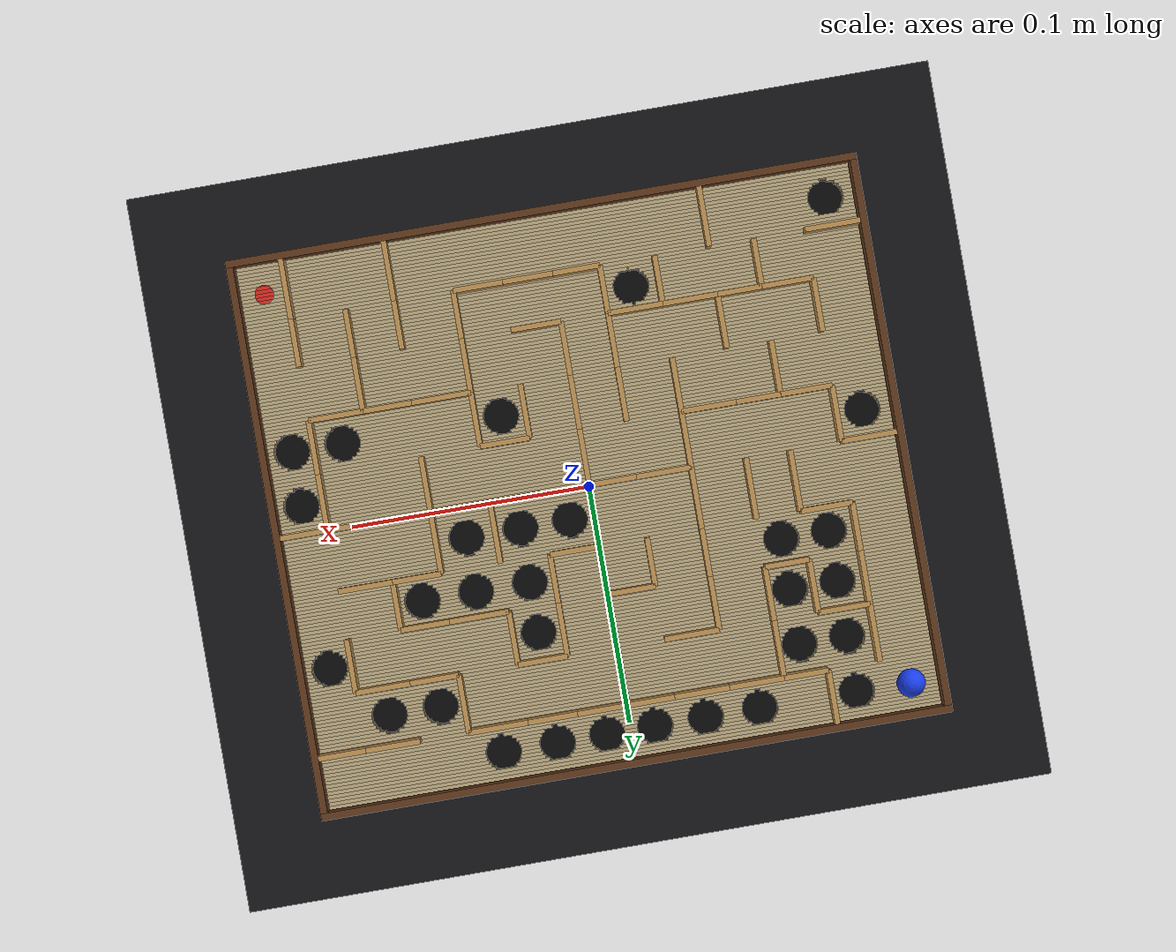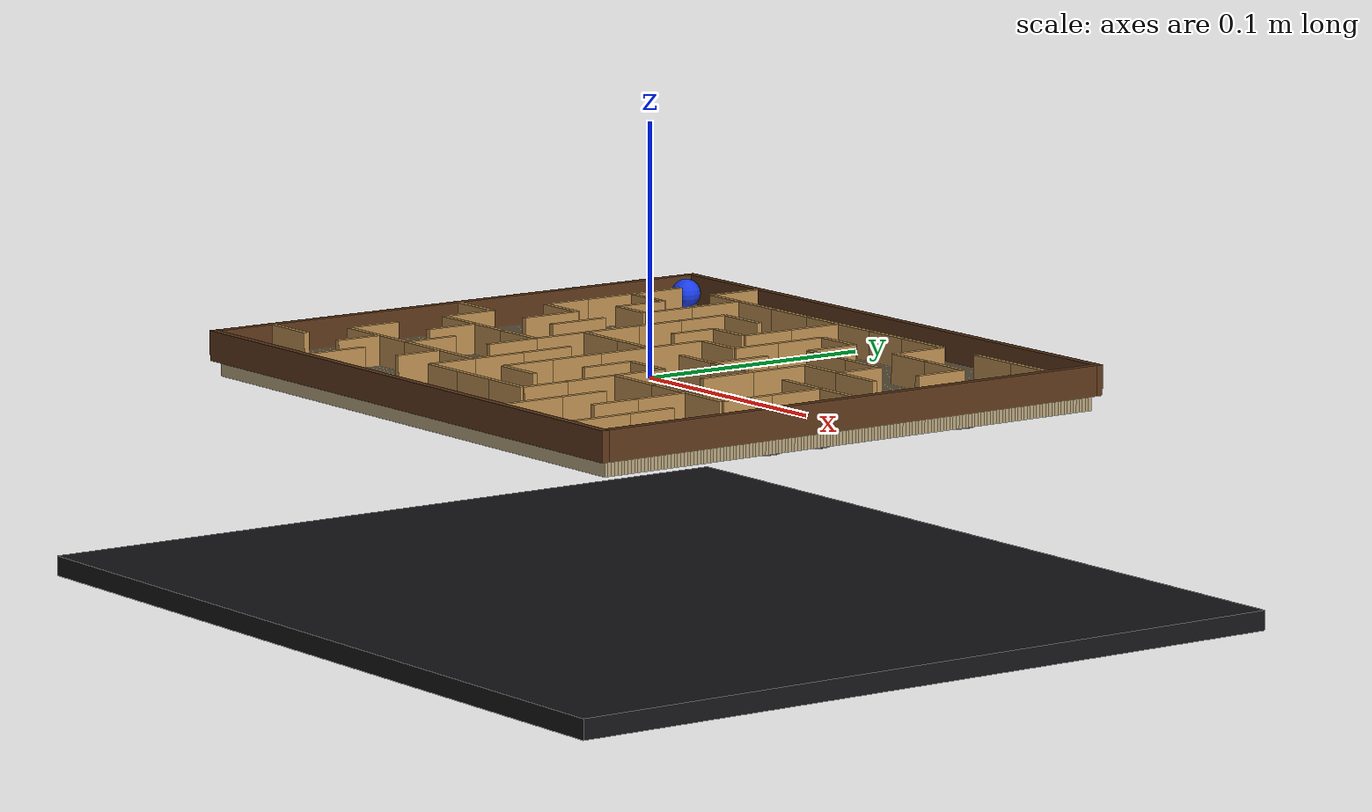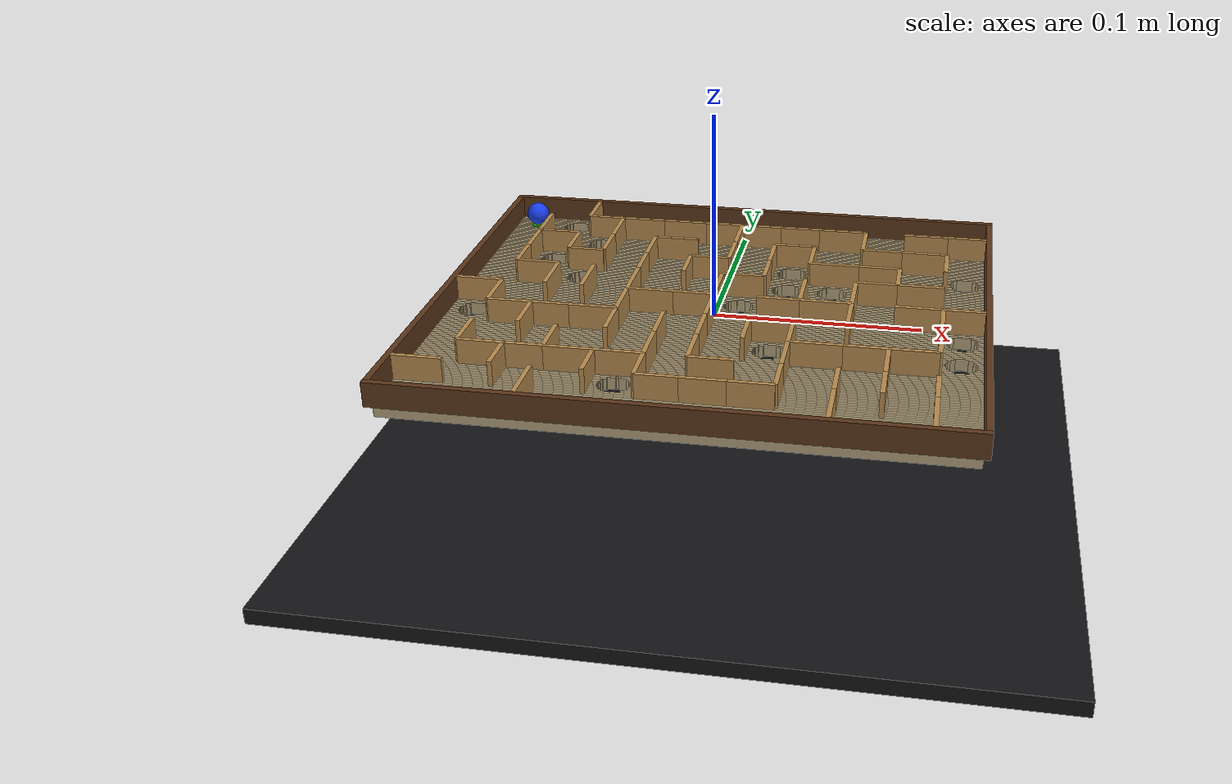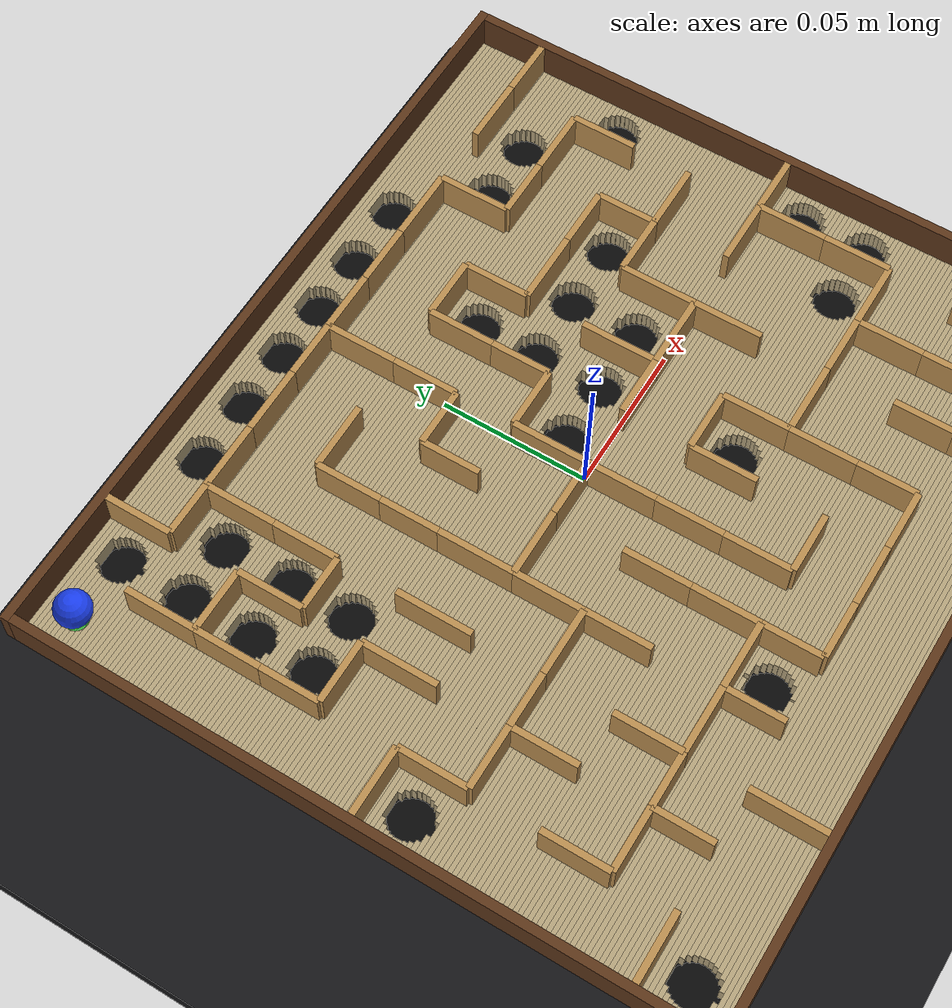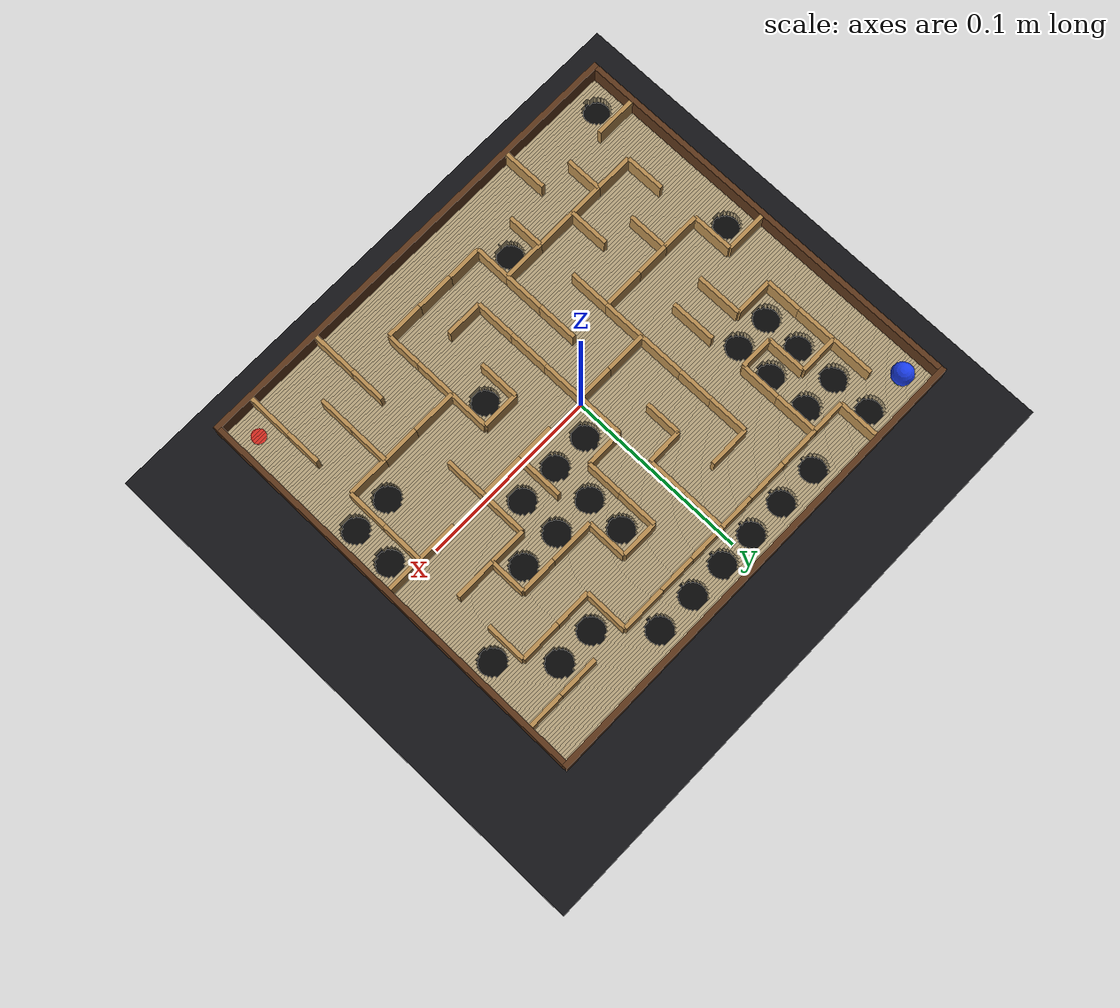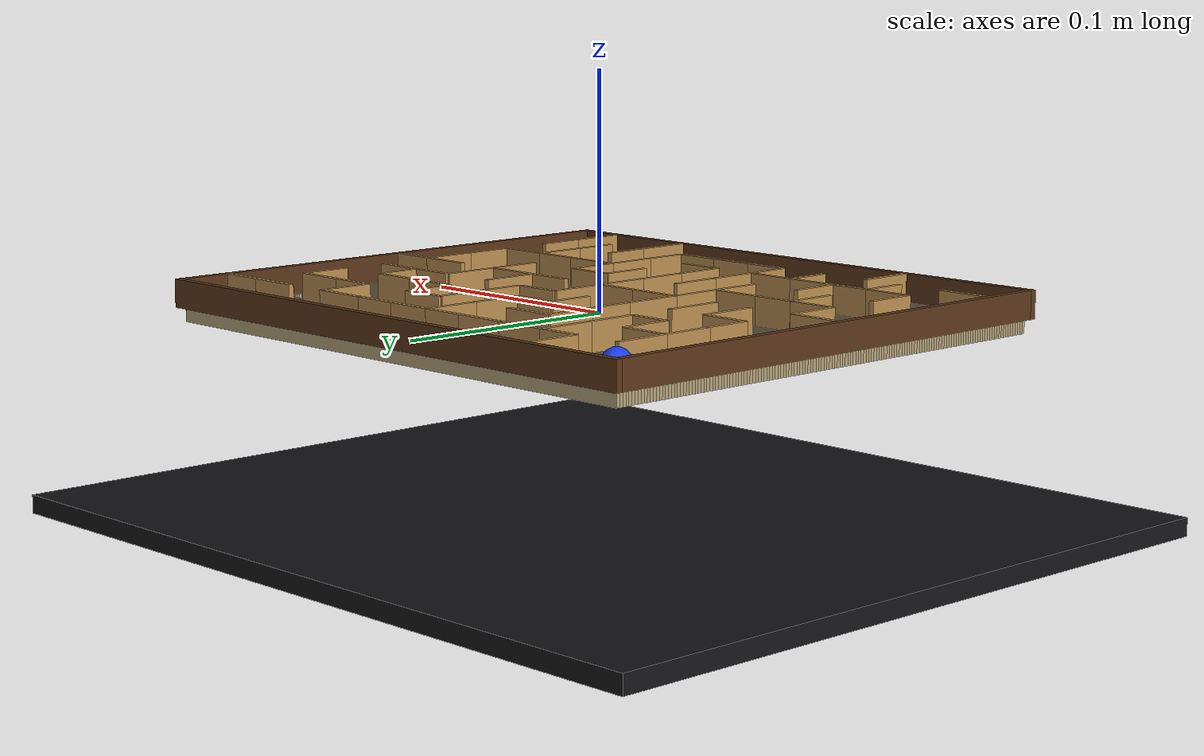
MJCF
<mujoco model="tag_custom_maze">
  <compiler angle="radian" inertiafromgeom="auto"/>
  <option timestep="0.001" gravity="0 0 -9.81" integrator="implicitfast" solver="Newton" iterations="12" tolerance="1e-9"/>
  <size nconmax="4000" njmax="12000"/>
  <visual>
    <global offwidth="900" offheight="800"/>
    <quality shadowsize="2048"/>
    <map znear="0.01" zfar="3"/>
  </visual>
  <default>
    <default class="floor">
      <geom friction="0.30 0.015 0.002" solref="0.004 1" solimp="0.95 0.99 0.001" density="650"/>
    </default>
    <default class="wall">
      <geom friction="0.35 0.02 0.003" solref="0.003 1" solimp="0.95 0.99 0.001" density="700"/>
    </default>
  </default>
  <worldbody>
    <light name="key" pos="0 -0.15 0.55" dir="0 0 -1" diffuse="0.9 0.9 0.9"/>
    <light name="fill" pos="-0.25 0.2 0.35" dir="0.4 -0.3 -1" diffuse="0.45 0.45 0.45"/>
    <camera name="top" pos="0 0 0.43" quat="1 0 0 0" mode="fixed" fovy="37"/>
    <geom name="catch_tray" type="box" pos="0 0 -0.085" size="0.18 0.16 0.004" rgba="0.08 0.08 0.09 1" friction="0.5 0.02 0.003"/>
    <body name="tilt_x_frame" pos="0 0 0">
      <inertial pos="0 0 0" mass="0.02" diaginertia="0.0001 0.0001 0.0001"/>
      <joint name="tilt_x" type="hinge" axis="1 0 0" range="-0.174532925 0.174532925" damping="0.8" armature="0.01"/>
      <body name="board" pos="0 0 0">
        <joint name="tilt_y" type="hinge" axis="0 1 0" range="-0.174532925 0.174532925" damping="0.8" armature="0.01"/>
        <geom name="floor_0" type="box" pos="0 -0.113751634 -0.003" size="0.1295 0.000748366013 0.003" rgba="0.70 0.63 0.48 1" class="floor"/><geom name="floor_1" type="box" pos="0 -0.112254902 -0.003" size="0.1295 0.000748366013 0.003" rgba="0.70 0.63 0.48 1" class="floor"/><geom name="floor_2" type="box" pos="0 -0.11075817 -0.003" size="0.1295 0.000748366013 0.003" rgba="0.70 0.63 0.48 1" class="floor"/><geom name="floor_3" type="box" pos="-0.12451748 -0.109261438 -0.003" size="0.00498252002 0.000748366013 0.003" rgba="0.70 0.63 0.48 1" class="floor"/><geom name="floor_4" type="box" pos="0.00661206994 -0.109261438 -0.003" size="0.12288793 0.000748366013 0.003" rgba="0.70 0.63 0.48 1" class="floor"/><geom name="floor_5" type="box" pos="-0.12606543 -0.107764706 -0.003" size="0.00343457035 0.000748366013 0.003" rgba="0.70 0.63 0.48 1" class="floor"/><geom name="floor_6" type="box" pos="0.00816001961 -0.107764706 -0.003" size="0.12133998 0.000748366013 0.003" rgba="0.70 0.63 0.48 1" class="floor"/><geom name="floor_7" type="box" pos="-0.126765543 -0.106267974 -0.003" size="0.00273445745 0.000748366013 0.003" rgba="0.70 0.63 0.48 1" class="floor"/><geom name="floor_8" type="box" pos="0.00886013251 -0.106267974 -0.003" size="0.120639867 0.000748366013 0.003" rgba="0.70 0.63 0.48 1" class="floor"/><geom name="floor_9" type="box" pos="-0.127175366 -0.104771242 -0.003" size="0.00232463369 0.000748366013 0.003" rgba="0.70 0.63 0.48 1" class="floor"/><geom name="floor_10" type="box" pos="0.00926995627 -0.104771242 -0.003" size="0.120230044 0.000748366013 0.003" rgba="0.70 0.63 0.48 1" class="floor"/><geom name="floor_11" type="box" pos="-0.127392919 -0.10327451 -0.003" size="0.00210708147 0.000748366013 0.003" rgba="0.70 0.63 0.48 1" class="floor"/><geom name="floor_12" type="box" pos="0.00948750849 -0.10327451 -0.003" size="0.120012492 0.000748366013 0.003" rgba="0.70 0.63 0.48 1" class="floor"/><geom name="floor_13" type="box" pos="-0.127451821 -0.101777778 -0.003" size="0.00204817886 0.000748366013 0.003" rgba="0.70 0.63 0.48 1" class="floor"/><geom name="floor_14" type="box" pos="0.0095464111 -0.101777778 -0.003" size="0.119953589 0.000748366013 0.003" rgba="0.70 0.63 0.48 1" class="floor"/><geom name="floor_15" type="box" pos="-0.127359748 -0.100281046 -0.003" size="0.00214025188 0.000748366013 0.003" rgba="0.70 0.63 0.48 1" class="floor"/><geom name="floor_16" type="box" pos="0.00945433808 -0.100281046 -0.003" size="0.120045662 0.000748366013 0.003" rgba="0.70 0.63 0.48 1" class="floor"/><geom name="floor_17" type="box" pos="-0.127104462 -0.0987843137 -0.003" size="0.00239553758 0.000748366013 0.003" rgba="0.70 0.63 0.48 1" class="floor"/><geom name="floor_18" type="box" pos="0.00919905238 -0.0987843137 -0.003" size="0.120300948 0.000748366013 0.003" rgba="0.70 0.63 0.48 1" class="floor"/><geom name="floor_19" type="box" pos="-0.126643766 -0.0972875817 -0.003" size="0.00285623408 0.000748366013 0.003" rgba="0.70 0.63 0.48 1" class="floor"/><geom name="floor_20" type="box" pos="0.00873835587 -0.0972875817 -0.003" size="0.120761644 0.000748366013 0.003" rgba="0.70 0.63 0.48 1" class="floor"/><geom name="floor_21" type="box" pos="-0.125849242 -0.0957908497 -0.003" size="0.00365075786 0.000748366013 0.003" rgba="0.70 0.63 0.48 1" class="floor"/><geom name="floor_22" type="box" pos="0.0079438321 -0.0957908497 -0.003" size="0.121556168 0.000748366013 0.003" rgba="0.70 0.63 0.48 1" class="floor"/><geom name="floor_23" type="box" pos="0 -0.0942941176 -0.003" size="0.1295 0.000748366013 0.003" rgba="0.70 0.63 0.48 1" class="floor"/><geom name="floor_24" type="box" pos="0 -0.0927973856 -0.003" size="0.1295 0.000748366013 0.003" rgba="0.70 0.63 0.48 1" class="floor"/><geom name="floor_25" type="box" pos="0 -0.0913006536 -0.003" size="0.1295 0.000748366013 0.003" rgba="0.70 0.63 0.48 1" class="floor"/><geom name="floor_26" type="box" pos="0 -0.0898039216 -0.003" size="0.1295 0.000748366013 0.003" rgba="0.70 0.63 0.48 1" class="floor"/><geom name="floor_27" type="box" pos="0 -0.0883071895 -0.003" size="0.1295 0.000748366013 0.003" rgba="0.70 0.63 0.48 1" class="floor"/><geom name="floor_28" type="box" pos="-0.0806940858 -0.0868104575 -0.003" size="0.0488059142 0.000748366013 0.003" rgba="0.70 0.63 0.48 1" class="floor"/><geom name="floor_29" type="box" pos="0.0490897516 -0.0868104575 -0.003" size="0.0804102484 0.000748366013 0.003" rgba="0.70 0.63 0.48 1" class="floor"/><geom name="floor_30" type="box" pos="-0.0828035697 -0.0853137255 -0.003" size="0.0466964303 0.000748366013 0.003" rgba="0.70 0.63 0.48 1" class="floor"/><geom name="floor_31" type="box" pos="0.0511992354 -0.0853137255 -0.003" size="0.0783007646 0.000748366013 0.003" rgba="0.70 0.63 0.48 1" class="floor"/><geom name="floor_32" type="box" pos="-0.0835517309 -0.0838169935 -0.003" size="0.0459482691 0.000748366013 0.003" rgba="0.70 0.63 0.48 1" class="floor"/><geom name="floor_33" type="box" pos="0.0519473966 -0.0838169935 -0.003" size="0.0775526034 0.000748366013 0.003" rgba="0.70 0.63 0.48 1" class="floor"/><geom name="floor_34" type="box" pos="-0.0839881311 -0.0823202614 -0.003" size="0.0455118689 0.000748366013 0.003" rgba="0.70 0.63 0.48 1" class="floor"/><geom name="floor_35" type="box" pos="0.0523837969 -0.0823202614 -0.003" size="0.0771162031 0.000748366013 0.003" rgba="0.70 0.63 0.48 1" class="floor"/><geom name="floor_36" type="box" pos="-0.0842256139 -0.0808235294 -0.003" size="0.0452743861 0.000748366013 0.003" rgba="0.70 0.63 0.48 1" class="floor"/><geom name="floor_37" type="box" pos="0.0526212796 -0.0808235294 -0.003" size="0.0768787204 0.000748366013 0.003" rgba="0.70 0.63 0.48 1" class="floor"/><geom name="floor_38" type="box" pos="-0.0843021631 -0.0793267974 -0.003" size="0.0451978369 0.000748366013 0.003" rgba="0.70 0.63 0.48 1" class="floor"/><geom name="floor_39" type="box" pos="0.0526978289 -0.0793267974 -0.003" size="0.0768021711 0.000748366013 0.003" rgba="0.70 0.63 0.48 1" class="floor"/><geom name="floor_40" type="box" pos="-0.0842278474 -0.0778300654 -0.003" size="0.0452721526 0.000748366013 0.003" rgba="0.70 0.63 0.48 1" class="floor"/><geom name="floor_41" type="box" pos="0.0526235132 -0.0778300654 -0.003" size="0.0768764868 0.000748366013 0.003" rgba="0.70 0.63 0.48 1" class="floor"/><geom name="floor_42" type="box" pos="-0.0839929051 -0.0763333333 -0.003" size="0.0455070949 0.000748366013 0.003" rgba="0.70 0.63 0.48 1" class="floor"/><geom name="floor_43" type="box" pos="0.0523885709 -0.0763333333 -0.003" size="0.0771114291 0.000748366013 0.003" rgba="0.70 0.63 0.48 1" class="floor"/><geom name="floor_44" type="box" pos="-0.0835599282 -0.0748366013 -0.003" size="0.0459400718 0.000748366013 0.003" rgba="0.70 0.63 0.48 1" class="floor"/><geom name="floor_45" type="box" pos="0.051955594 -0.0748366013 -0.003" size="0.077544406 0.000748366013 0.003" rgba="0.70 0.63 0.48 1" class="floor"/><geom name="floor_46" type="box" pos="-0.0828181045 -0.0733398693 -0.003" size="0.0466818955 0.000748366013 0.003" rgba="0.70 0.63 0.48 1" class="floor"/><geom name="floor_47" type="box" pos="0.0512137703 -0.0733398693 -0.003" size="0.0782862297 0.000748366013 0.003" rgba="0.70 0.63 0.48 1" class="floor"/><geom name="floor_48" type="box" pos="-0.0808718771 -0.0718431373 -0.003" size="0.0486281229 0.000748366013 0.003" rgba="0.70 0.63 0.48 1" class="floor"/><geom name="floor_49" type="box" pos="0.0492675428 -0.0718431373 -0.003" size="0.0802324572 0.000748366013 0.003" rgba="0.70 0.63 0.48 1" class="floor"/><geom name="floor_50" type="box" pos="0 -0.0703464052 -0.003" size="0.1295 0.000748366013 0.003" rgba="0.70 0.63 0.48 1" class="floor"/><geom name="floor_51" type="box" pos="0 -0.0688496732 -0.003" size="0.1295 0.000748366013 0.003" rgba="0.70 0.63 0.48 1" class="floor"/><geom name="floor_52" type="box" pos="0 -0.0673529412 -0.003" size="0.1295 0.000748366013 0.003" rgba="0.70 0.63 0.48 1" class="floor"/><geom name="floor_53" type="box" pos="0 -0.0658562092 -0.003" size="0.1295 0.000748366013 0.003" rgba="0.70 0.63 0.48 1" class="floor"/><geom name="floor_54" type="box" pos="0 -0.0643594771 -0.003" size="0.1295 0.000748366013 0.003" rgba="0.70 0.63 0.48 1" class="floor"/><geom name="floor_55" type="box" pos="0 -0.0628627451 -0.003" size="0.1295 0.000748366013 0.003" rgba="0.70 0.63 0.48 1" class="floor"/><geom name="floor_56" type="box" pos="0 -0.0613660131 -0.003" size="0.1295 0.000748366013 0.003" rgba="0.70 0.63 0.48 1" class="floor"/><geom name="floor_57" type="box" pos="0 -0.059869281 -0.003" size="0.1295 0.000748366013 0.003" rgba="0.70 0.63 0.48 1" class="floor"/><geom name="floor_58" type="box" pos="0 -0.058372549 -0.003" size="0.1295 0.000748366013 0.003" rgba="0.70 0.63 0.48 1" class="floor"/><geom name="floor_59" type="box" pos="0 -0.056875817 -0.003" size="0.1295 0.000748366013 0.003" rgba="0.70 0.63 0.48 1" class="floor"/><geom name="floor_60" type="box" pos="0 -0.055379085 -0.003" size="0.1295 0.000748366013 0.003" rgba="0.70 0.63 0.48 1" class="floor"/><geom name="floor_61" type="box" pos="0 -0.0538823529 -0.003" size="0.1295 0.000748366013 0.003" rgba="0.70 0.63 0.48 1" class="floor"/><geom name="floor_62" type="box" pos="0 -0.0523856209 -0.003" size="0.1295 0.000748366013 0.003" rgba="0.70 0.63 0.48 1" class="floor"/><geom name="floor_63" type="box" pos="0 -0.0508888889 -0.003" size="0.1295 0.000748366013 0.003" rgba="0.70 0.63 0.48 1" class="floor"/><geom name="floor_64" type="box" pos="0 -0.0493921569 -0.003" size="0.1295 0.000748366013 0.003" rgba="0.70 0.63 0.48 1" class="floor"/><geom name="floor_65" type="box" pos="0 -0.0478954248 -0.003" size="0.1295 0.000748366013 0.003" rgba="0.70 0.63 0.48 1" class="floor"/><geom name="floor_66" type="box" pos="0 -0.0463986928 -0.003" size="0.1295 0.000748366013 0.003" rgba="0.70 0.63 0.48 1" class="floor"/><geom name="floor_67" type="box" pos="0 -0.0449019608 -0.003" size="0.1295 0.000748366013 0.003" rgba="0.70 0.63 0.48 1" class="floor"/><geom name="floor_68" type="box" pos="0 -0.0434052288 -0.003" size="0.1295 0.000748366013 0.003" rgba="0.70 0.63 0.48 1" class="floor"/><geom name="floor_69" type="box" pos="-0.0510056536 -0.0419084967 -0.003" size="0.0784943464 0.000748366013 0.003" rgba="0.70 0.63 0.48 1" class="floor"/><geom name="floor_70" type="box" pos="0.0646393309 -0.0419084967 -0.003" size="0.0299642092 0.000748366013 0.003" rgba="0.70 0.63 0.48 1" class="floor"/><geom name="floor_71" type="box" pos="0.108880294 -0.0419084967 -0.003" size="0.00709032498 0.000748366013 0.003" rgba="0.70 0.63 0.48 1" class="floor"/><geom name="floor_72" type="box" pos="0.126328524 -0.0419084967 -0.003" size="0.00317147601 0.000748366013 0.003" rgba="0.70 0.63 0.48 1" class="floor"/><geom name="floor_73" type="box" pos="-0.0519648413 -0.0404117647 -0.003" size="0.0775351587 0.000748366013 0.003" rgba="0.70 0.63 0.48 1" class="floor"/><geom name="floor_74" type="box" pos="0.0646393309 -0.0404117647 -0.003" size="0.028045834 0.000748366013 0.003" rgba="0.70 0.63 0.48 1" class="floor"/><geom name="floor_75" type="box" pos="0.108880294 -0.0404117647 -0.003" size="0.00517194971 0.000748366013 0.003" rgba="0.70 0.63 0.48 1" class="floor"/><geom name="floor_76" type="box" pos="0.127287712 -0.0404117647 -0.003" size="0.00221228838 0.000748366013 0.003" rgba="0.70 0.63 0.48 1" class="floor"/><geom name="floor_77" type="box" pos="-0.0525016001 -0.0389150327 -0.003" size="0.0769983999 0.000748366013 0.003" rgba="0.70 0.63 0.48 1" class="floor"/><geom name="floor_78" type="box" pos="0.0646393309 -0.0389150327 -0.003" size="0.0269723163 0.000748366013 0.003" rgba="0.70 0.63 0.48 1" class="floor"/><geom name="floor_79" type="box" pos="0.108880294 -0.0389150327 -0.003" size="0.00409843208 0.000748366013 0.003" rgba="0.70 0.63 0.48 1" class="floor"/><geom name="floor_80" type="box" pos="0.12782447 -0.0389150327 -0.003" size="0.00167552957 0.000748366013 0.003" rgba="0.70 0.63 0.48 1" class="floor"/><geom name="floor_81" type="box" pos="-0.0528100616 -0.0374183007 -0.003" size="0.0766899384 0.000748366013 0.003" rgba="0.70 0.63 0.48 1" class="floor"/><geom name="floor_82" type="box" pos="0.0646393309 -0.0374183007 -0.003" size="0.0263553932 0.000748366013 0.003" rgba="0.70 0.63 0.48 1" class="floor"/><geom name="floor_83" type="box" pos="0.108880294 -0.0374183007 -0.003" size="0.00348150896 0.000748366013 0.003" rgba="0.70 0.63 0.48 1" class="floor"/><geom name="floor_84" type="box" pos="0.128132932 -0.0374183007 -0.003" size="0.001367068 0.000748366013 0.003" rgba="0.70 0.63 0.48 1" class="floor"/><geom name="floor_85" type="box" pos="-0.0529471754 -0.0359215686 -0.003" size="0.0765528246 0.000748366013 0.003" rgba="0.70 0.63 0.48 1" class="floor"/><geom name="floor_86" type="box" pos="0.0646393309 -0.0359215686 -0.003" size="0.0260811657 0.000748366013 0.003" rgba="0.70 0.63 0.48 1" class="floor"/><geom name="floor_87" type="box" pos="0.108880294 -0.0359215686 -0.003" size="0.00320728144 0.000748366013 0.003" rgba="0.70 0.63 0.48 1" class="floor"/><geom name="floor_88" type="box" pos="0.128270046 -0.0359215686 -0.003" size="0.00122995425 0.000748366013 0.003" rgba="0.70 0.63 0.48 1" class="floor"/><geom name="floor_89" type="box" pos="-0.052931922 -0.0344248366 -0.003" size="0.076568078 0.000748366013 0.003" rgba="0.70 0.63 0.48 1" class="floor"/><geom name="floor_90" type="box" pos="0.0646393309 -0.0344248366 -0.003" size="0.0261116725 0.000748366013 0.003" rgba="0.70 0.63 0.48 1" class="floor"/><geom name="floor_91" type="box" pos="0.108880294 -0.0344248366 -0.003" size="0.00323778825 0.000748366013 0.003" rgba="0.70 0.63 0.48 1" class="floor"/><geom name="floor_92" type="box" pos="0.128254792 -0.0344248366 -0.003" size="0.00124520765 0.000748366013 0.003" rgba="0.70 0.63 0.48 1" class="floor"/><geom name="floor_93" type="box" pos="-0.0527623398 -0.0329281046 -0.003" size="0.0767376602 0.000748366013 0.003" rgba="0.70 0.63 0.48 1" class="floor"/><geom name="floor_94" type="box" pos="0.0646393309 -0.0329281046 -0.003" size="0.026450837 0.000748366013 0.003" rgba="0.70 0.63 0.48 1" class="floor"/><geom name="floor_95" type="box" pos="0.108880294 -0.0329281046 -0.003" size="0.00357695275 0.000748366013 0.003" rgba="0.70 0.63 0.48 1" class="floor"/><geom name="floor_96" type="box" pos="0.12808521 -0.0329281046 -0.003" size="0.0014147899 0.000748366013 0.003" rgba="0.70 0.63 0.48 1" class="floor"/><geom name="floor_97" type="box" pos="-0.052414024 -0.0314313725 -0.003" size="0.077085976 0.000748366013 0.003" rgba="0.70 0.63 0.48 1" class="floor"/><geom name="floor_98" type="box" pos="0.0646393309 -0.0314313725 -0.003" size="0.0271474686 0.000748366013 0.003" rgba="0.70 0.63 0.48 1" class="floor"/><geom name="floor_99" type="box" pos="0.108880294 -0.0314313725 -0.003" size="0.00427358434 0.000748366013 0.003" rgba="0.70 0.63 0.48 1" class="floor"/><geom name="floor_100" type="box" pos="0.127736894 -0.0314313725 -0.003" size="0.00176310569 0.000748366013 0.003" rgba="0.70 0.63 0.48 1" class="floor"/><geom name="floor_101" type="box" pos="-0.0518162988 -0.0299346405 -0.003" size="0.0776837012 0.000748366013 0.003" rgba="0.70 0.63 0.48 1" class="floor"/><geom name="floor_102" type="box" pos="0.0646393309 -0.0299346405 -0.003" size="0.0283429188 0.000748366013 0.003" rgba="0.70 0.63 0.48 1" class="floor"/><geom name="floor_103" type="box" pos="0.108880294 -0.0299346405 -0.003" size="0.00546903458 0.000748366013 0.003" rgba="0.70 0.63 0.48 1" class="floor"/><geom name="floor_104" type="box" pos="0.127139169 -0.0299346405 -0.003" size="0.00236083081 0.000748366013 0.003" rgba="0.70 0.63 0.48 1" class="floor"/><geom name="floor_105" type="box" pos="-0.050693481 -0.0284379085 -0.003" size="0.078806519 0.000748366013 0.003" rgba="0.70 0.63 0.48 1" class="floor"/><geom name="floor_106" type="box" pos="0.0646393309 -0.0284379085 -0.003" size="0.0305885545 0.000748366013 0.003" rgba="0.70 0.63 0.48 1" class="floor"/><geom name="floor_107" type="box" pos="0.108880294 -0.0284379085 -0.003" size="0.00771467029 0.000748366013 0.003" rgba="0.70 0.63 0.48 1" class="floor"/><geom name="floor_108" type="box" pos="0.126016351 -0.0284379085 -0.003" size="0.00348364867 0.000748366013 0.003" rgba="0.70 0.63 0.48 1" class="floor"/><geom name="floor_109" type="box" pos="0 -0.0269411765 -0.003" size="0.1295 0.000748366013 0.003" rgba="0.70 0.63 0.48 1" class="floor"/><geom name="floor_110" type="box" pos="0 -0.0254444444 -0.003" size="0.1295 0.000748366013 0.003" rgba="0.70 0.63 0.48 1" class="floor"/><geom name="floor_111" type="box" pos="0 -0.0239477124 -0.003" size="0.1295 0.000748366013 0.003" rgba="0.70 0.63 0.48 1" class="floor"/><geom name="floor_112" type="box" pos="0 -0.0224509804 -0.003" size="0.1295 0.000748366013 0.003" rgba="0.70 0.63 0.48 1" class="floor"/><geom name="floor_113" type="box" pos="0 -0.0209542484 -0.003" size="0.1295 0.000748366013 0.003" rgba="0.70 0.63 0.48 1" class="floor"/><geom name="floor_114" type="box" pos="-0.124810176 -0.0194575163 -0.003" size="0.00468982448 0.000748366013 0.003" rgba="0.70 0.63 0.48 1" class="floor"/><geom name="floor_115" type="box" pos="0.000829211729 -0.0194575163 -0.003" size="0.116519681 0.000748366013 0.003" rgba="0.70 0.63 0.48 1" class="floor"/><geom name="floor_116" type="box" pos="0.125639387 -0.0194575163 -0.003" size="0.00386061275 0.000748366013 0.003" rgba="0.70 0.63 0.48 1" class="floor"/><geom name="floor_117" type="box" pos="-0.126158074 -0.0179607843 -0.003" size="0.00334192588 0.000748366013 0.003" rgba="0.70 0.63 0.48 1" class="floor"/><geom name="floor_118" type="box" pos="0.000829211729 -0.0179607843 -0.003" size="0.113823884 0.000748366013 0.003" rgba="0.70 0.63 0.48 1" class="floor"/><geom name="floor_119" type="box" pos="0.126987286 -0.0179607843 -0.003" size="0.00251271415 0.000748366013 0.003" rgba="0.70 0.63 0.48 1" class="floor"/><geom name="floor_120" type="box" pos="-0.126818966 -0.0164640523 -0.003" size="0.00268103431 0.000748366013 0.003" rgba="0.70 0.63 0.48 1" class="floor"/><geom name="floor_121" type="box" pos="0.000829211729 -0.0164640523 -0.003" size="0.1125021 0.000748366013 0.003" rgba="0.70 0.63 0.48 1" class="floor"/><geom name="floor_122" type="box" pos="0.127648177 -0.0164640523 -0.003" size="0.00185182259 0.000748366013 0.003" rgba="0.70 0.63 0.48 1" class="floor"/><geom name="floor_123" type="box" pos="-0.127206021 -0.0149673203 -0.003" size="0.00229397937 0.000748366013 0.003" rgba="0.70 0.63 0.48 1" class="floor"/><geom name="floor_124" type="box" pos="0.000829211729 -0.0149673203 -0.003" size="0.111727991 0.000748366013 0.003" rgba="0.70 0.63 0.48 1" class="floor"/><geom name="floor_125" type="box" pos="0.128035232 -0.0149673203 -0.003" size="0.00146476764 0.000748366013 0.003" rgba="0.70 0.63 0.48 1" class="floor"/><geom name="floor_126" type="box" pos="-0.127406117 -0.0134705882 -0.003" size="0.00209388349 0.000748366013 0.003" rgba="0.70 0.63 0.48 1" class="floor"/><geom name="floor_127" type="box" pos="0.000829211729 -0.0134705882 -0.003" size="0.111327799 0.000748366013 0.003" rgba="0.70 0.63 0.48 1" class="floor"/><geom name="floor_128" type="box" pos="0.128235328 -0.0134705882 -0.003" size="0.00126467176 0.000748366013 0.003" rgba="0.70 0.63 0.48 1" class="floor"/><geom name="floor_129" type="box" pos="-0.127449329 -0.0119738562 -0.003" size="0.00205067122 0.000748366013 0.003" rgba="0.70 0.63 0.48 1" class="floor"/><geom name="floor_130" type="box" pos="0.000829211729 -0.0119738562 -0.003" size="0.111241374 0.000748366013 0.003" rgba="0.70 0.63 0.48 1" class="floor"/><geom name="floor_131" type="box" pos="0.128278541 -0.0119738562 -0.003" size="0.00122145949 0.000748366013 0.003" rgba="0.70 0.63 0.48 1" class="floor"/><geom name="floor_132" type="box" pos="-0.127341251 -0.0104771242 -0.003" size="0.00215874867 0.000748366013 0.003" rgba="0.70 0.63 0.48 1" class="floor"/><geom name="floor_133" type="box" pos="0.000829211729 -0.0104771242 -0.003" size="0.111457529 0.000748366013 0.003" rgba="0.70 0.63 0.48 1" class="floor"/><geom name="floor_134" type="box" pos="0.128170463 -0.0104771242 -0.003" size="0.00132953695 0.000748366013 0.003" rgba="0.70 0.63 0.48 1" class="floor"/><geom name="floor_135" type="box" pos="-0.127067337 -0.00898039216 -0.003" size="0.00243266343 0.000748366013 0.003" rgba="0.70 0.63 0.48 1" class="floor"/><geom name="floor_136" type="box" pos="0.000829211729 -0.00898039216 -0.003" size="0.112005359 0.000748366013 0.003" rgba="0.70 0.63 0.48 1" class="floor"/><geom name="floor_137" type="box" pos="0.127896548 -0.00898039216 -0.003" size="0.00160345171 0.000748366013 0.003" rgba="0.70 0.63 0.48 1" class="floor"/><geom name="floor_138" type="box" pos="-0.126580615 -0.00748366013 -0.003" size="0.00291938458 0.000748366013 0.003" rgba="0.70 0.63 0.48 1" class="floor"/><geom name="floor_139" type="box" pos="0.000829211729 -0.00748366013 -0.003" size="0.112978801 0.000748366013 0.003" rgba="0.70 0.63 0.48 1" class="floor"/><geom name="floor_140" type="box" pos="0.127409827 -0.00748366013 -0.003" size="0.00209017285 0.000748366013 0.003" rgba="0.70 0.63 0.48 1" class="floor"/><geom name="floor_141" type="box" pos="-0.125733441 -0.0059869281 -0.003" size="0.00376655922 0.000748366013 0.003" rgba="0.70 0.63 0.48 1" class="floor"/><geom name="floor_142" type="box" pos="0.000829211729 -0.0059869281 -0.003" size="0.11467315 0.000748366013 0.003" rgba="0.70 0.63 0.48 1" class="floor"/><geom name="floor_143" type="box" pos="0.126562653 -0.0059869281 -0.003" size="0.00293734749 0.000748366013 0.003" rgba="0.70 0.63 0.48 1" class="floor"/><geom name="floor_144" type="box" pos="0 -0.00449019608 -0.003" size="0.1295 0.000748366013 0.003" rgba="0.70 0.63 0.48 1" class="floor"/><geom name="floor_145" type="box" pos="0 -0.00299346405 -0.003" size="0.1295 0.000748366013 0.003" rgba="0.70 0.63 0.48 1" class="floor"/><geom name="floor_146" type="box" pos="0 -0.00149673203 -0.003" size="0.1295 0.000748366013 0.003" rgba="0.70 0.63 0.48 1" class="floor"/><geom name="floor_147" type="box" pos="0 -1.38777878e-17 -0.003" size="0.1295 0.000748366013 0.003" rgba="0.70 0.63 0.48 1" class="floor"/><geom name="floor_148" type="box" pos="0 0.00149673203 -0.003" size="0.1295 0.000748366013 0.003" rgba="0.70 0.63 0.48 1" class="floor"/><geom name="floor_149" type="box" pos="0 0.00299346405 -0.003" size="0.1295 0.000748366013 0.003" rgba="0.70 0.63 0.48 1" class="floor"/><geom name="floor_150" type="box" pos="0 0.00449019608 -0.003" size="0.1295 0.000748366013 0.003" rgba="0.70 0.63 0.48 1" class="floor"/><geom name="floor_151" type="box" pos="-0.0616968838 0.0059869281 -0.003" size="0.0678031162 0.000748366013 0.003" rgba="0.70 0.63 0.48 1" class="floor"/><geom name="floor_152" type="box" pos="0.0206382219 0.0059869281 -0.003" size="0.00635538112 0.000748366013 0.003" rgba="0.70 0.63 0.48 1" class="floor"/><geom name="floor_153" type="box" pos="0.0425022119 0.0059869281 -0.003" size="0.00733200048 0.000748366013 0.003" rgba="0.70 0.63 0.48 1" class="floor"/><geom name="floor_154" type="box" pos="0.0937554104 0.0059869281 -0.003" size="0.0357445896 0.000748366013 0.003" rgba="0.70 0.63 0.48 1" class="floor"/><geom name="floor_155" type="box" pos="-0.0625378734 0.00748366013 -0.003" size="0.0669621266 0.000748366013 0.003" rgba="0.70 0.63 0.48 1" class="floor"/><geom name="floor_156" type="box" pos="0.0206382219 0.00748366013 -0.003" size="0.00467340191 0.000748366013 0.003" rgba="0.70 0.63 0.48 1" class="floor"/><geom name="floor_157" type="box" pos="0.0425022119 0.00748366013 -0.003" size="0.00565002127 0.000748366013 0.003" rgba="0.70 0.63 0.48 1" class="floor"/><geom name="floor_158" type="box" pos="0.0945964 0.00748366013 -0.003" size="0.0349036 0.000748366013 0.003" rgba="0.70 0.63 0.48 1" class="floor"/><geom name="floor_159" type="box" pos="-0.0630216223 0.00898039216 -0.003" size="0.0664783777 0.000748366013 0.003" rgba="0.70 0.63 0.48 1" class="floor"/><geom name="floor_160" type="box" pos="0.0206382219 0.00898039216 -0.003" size="0.00370590404 0.000748366013 0.003" rgba="0.70 0.63 0.48 1" class="floor"/><geom name="floor_161" type="box" pos="0.0425022119 0.00898039216 -0.003" size="0.0046825234 0.000748366013 0.003" rgba="0.70 0.63 0.48 1" class="floor"/><geom name="floor_162" type="box" pos="0.0950801489 0.00898039216 -0.003" size="0.0344198511 0.000748366013 0.003" rgba="0.70 0.63 0.48 1" class="floor"/><geom name="floor_163" type="box" pos="-0.0632934325 0.0104771242 -0.003" size="0.0662065675 0.000748366013 0.003" rgba="0.70 0.63 0.48 1" class="floor"/><geom name="floor_164" type="box" pos="0.0206382219 0.0104771242 -0.003" size="0.00316228374 0.000748366013 0.003" rgba="0.70 0.63 0.48 1" class="floor"/><geom name="floor_165" type="box" pos="0.0425022119 0.0104771242 -0.003" size="0.0041389031 0.000748366013 0.003" rgba="0.70 0.63 0.48 1" class="floor"/><geom name="floor_166" type="box" pos="0.095351959 0.0104771242 -0.003" size="0.034148041 0.000748366013 0.003" rgba="0.70 0.63 0.48 1" class="floor"/><geom name="floor_167" type="box" pos="-0.0633997141 0.0119738562 -0.003" size="0.0661002859 0.000748366013 0.003" rgba="0.70 0.63 0.48 1" class="floor"/><geom name="floor_168" type="box" pos="0.0206382219 0.0119738562 -0.003" size="0.00294972056 0.000748366013 0.003" rgba="0.70 0.63 0.48 1" class="floor"/><geom name="floor_169" type="box" pos="0.0425022119 0.0119738562 -0.003" size="0.00392633992 0.000748366013 0.003" rgba="0.70 0.63 0.48 1" class="floor"/><geom name="floor_170" type="box" pos="0.0954582406 0.0119738562 -0.003" size="0.0340417594 0.000748366013 0.003" rgba="0.70 0.63 0.48 1" class="floor"/><geom name="floor_171" type="box" pos="-0.0633547512 0.0134705882 -0.003" size="0.0661452488 0.000748366013 0.003" rgba="0.70 0.63 0.48 1" class="floor"/><geom name="floor_172" type="box" pos="0.0206382219 0.0134705882 -0.003" size="0.00303964634 0.000748366013 0.003" rgba="0.70 0.63 0.48 1" class="floor"/><geom name="floor_173" type="box" pos="0.0425022119 0.0134705882 -0.003" size="0.0040162657 0.000748366013 0.003" rgba="0.70 0.63 0.48 1" class="floor"/><geom name="floor_174" type="box" pos="0.0954132777 0.0134705882 -0.003" size="0.0340867223 0.000748366013 0.003" rgba="0.70 0.63 0.48 1" class="floor"/><geom name="floor_175" type="box" pos="-0.0631527197 0.0149673203 -0.003" size="0.0663472803 0.000748366013 0.003" rgba="0.70 0.63 0.48 1" class="floor"/><geom name="floor_176" type="box" pos="0.0206382219 0.0149673203 -0.003" size="0.00344370924 0.000748366013 0.003" rgba="0.70 0.63 0.48 1" class="floor"/><geom name="floor_177" type="box" pos="0.0425022119 0.0149673203 -0.003" size="0.0044203286 0.000748366013 0.003" rgba="0.70 0.63 0.48 1" class="floor"/><geom name="floor_178" type="box" pos="0.0952112463 0.0149673203 -0.003" size="0.0342887537 0.000748366013 0.003" rgba="0.70 0.63 0.48 1" class="floor"/><geom name="floor_179" type="box" pos="-0.0627631627 0.0164640523 -0.003" size="0.0667368373 0.000748366013 0.003" rgba="0.70 0.63 0.48 1" class="floor"/><geom name="floor_180" type="box" pos="0.0206382219 0.0164640523 -0.003" size="0.00422282337 0.000748366013 0.003" rgba="0.70 0.63 0.48 1" class="floor"/><geom name="floor_181" type="box" pos="0.0425022119 0.0164640523 -0.003" size="0.00519944273 0.000748366013 0.003" rgba="0.70 0.63 0.48 1" class="floor"/><geom name="floor_182" type="box" pos="0.0948216892 0.0164640523 -0.003" size="0.0346783108 0.000748366013 0.003" rgba="0.70 0.63 0.48 1" class="floor"/><geom name="floor_183" type="box" pos="-0.0620980419 0.0179607843 -0.003" size="0.0674019581 0.000748366013 0.003" rgba="0.70 0.63 0.48 1" class="floor"/><geom name="floor_184" type="box" pos="0.0206382219 0.0179607843 -0.003" size="0.0055530649 0.000748366013 0.003" rgba="0.70 0.63 0.48 1" class="floor"/><geom name="floor_185" type="box" pos="0.0425022119 0.0179607843 -0.003" size="0.00652968426 0.000748366013 0.003" rgba="0.70 0.63 0.48 1" class="floor"/><geom name="floor_186" type="box" pos="0.0941565685 0.0179607843 -0.003" size="0.0353434315 0.000748366013 0.003" rgba="0.70 0.63 0.48 1" class="floor"/><geom name="floor_187" type="box" pos="-0.0607317126 0.0194575163 -0.003" size="0.0687682874 0.000748366013 0.003" rgba="0.70 0.63 0.48 1" class="floor"/><geom name="floor_188" type="box" pos="0.0206382219 0.0194575163 -0.003" size="0.00828572347 0.000748366013 0.003" rgba="0.70 0.63 0.48 1" class="floor"/><geom name="floor_189" type="box" pos="0.0425022119 0.0194575163 -0.003" size="0.00926234283 0.000748366013 0.003" rgba="0.70 0.63 0.48 1" class="floor"/><geom name="floor_190" type="box" pos="0.0927902392 0.0194575163 -0.003" size="0.0367097608 0.000748366013 0.003" rgba="0.70 0.63 0.48 1" class="floor"/><geom name="floor_191" type="box" pos="0 0.0209542484 -0.003" size="0.1295 0.000748366013 0.003" rgba="0.70 0.63 0.48 1" class="floor"/><geom name="floor_192" type="box" pos="0 0.0224509804 -0.003" size="0.1295 0.000748366013 0.003" rgba="0.70 0.63 0.48 1" class="floor"/><geom name="floor_193" type="box" pos="0 0.0239477124 -0.003" size="0.1295 0.000748366013 0.003" rgba="0.70 0.63 0.48 1" class="floor"/><geom name="floor_194" type="box" pos="0 0.0254444444 -0.003" size="0.1295 0.000748366013 0.003" rgba="0.70 0.63 0.48 1" class="floor"/><geom name="floor_195" type="box" pos="0 0.0269411765 -0.003" size="0.1295 0.000748366013 0.003" rgba="0.70 0.63 0.48 1" class="floor"/><geom name="floor_196" type="box" pos="-0.114110843 0.0284379085 -0.003" size="0.0153891575 0.000748366013 0.003" rgba="0.70 0.63 0.48 1" class="floor"/><geom name="floor_197" type="box" pos="-0.0854516286 0.0284379085 -0.003" size="0.00683610752 0.000748366013 0.003" rgba="0.70 0.63 0.48 1" class="floor"/><geom name="floor_198" type="box" pos="-0.0221583197 0.0284379085 -0.003" size="0.0500232525 0.000748366013 0.003" rgba="0.70 0.63 0.48 1" class="floor"/><geom name="floor_199" type="box" pos="0.0425022119 0.0284379085 -0.003" size="0.00820333022 0.000748366013 0.003" rgba="0.70 0.63 0.48 1" class="floor"/><geom name="floor_200" type="box" pos="0.0652452909 0.0284379085 -0.003" size="0.00810579993 0.000748366013 0.003" rgba="0.70 0.63 0.48 1" class="floor"/><geom name="floor_201" type="box" pos="0.10464252 0.0284379085 -0.003" size="0.0248574801 0.000748366013 0.003" rgba="0.70 0.63 0.48 1" class="floor"/><geom name="floor_202" type="box" pos="-0.115166447 0.0299346405 -0.003" size="0.0143335531 0.000748366013 0.003" rgba="0.70 0.63 0.48 1" class="floor"/><geom name="floor_203" type="box" pos="-0.0854516286 0.0299346405 -0.003" size="0.00472489876 0.000748366013 0.003" rgba="0.70 0.63 0.48 1" class="floor"/><geom name="floor_204" type="box" pos="-0.0221583197 0.0299346405 -0.003" size="0.0479120437 0.000748366013 0.003" rgba="0.70 0.63 0.48 1" class="floor"/><geom name="floor_205" type="box" pos="0.0425022119 0.0299346405 -0.003" size="0.00609212146 0.000748366013 0.003" rgba="0.70 0.63 0.48 1" class="floor"/><geom name="floor_206" type="box" pos="0.0652452909 0.0299346405 -0.003" size="0.00599459117 0.000748366013 0.003" rgba="0.70 0.63 0.48 1" class="floor"/><geom name="floor_207" type="box" pos="0.105698124 0.0299346405 -0.003" size="0.0238018758 0.000748366013 0.003" rgba="0.70 0.63 0.48 1" class="floor"/><geom name="floor_208" type="box" pos="-0.115740786 0.0314313725 -0.003" size="0.013759214 0.000748366013 0.003" rgba="0.70 0.63 0.48 1" class="floor"/><geom name="floor_209" type="box" pos="-0.0854516286 0.0314313725 -0.003" size="0.0035762205 0.000748366013 0.003" rgba="0.70 0.63 0.48 1" class="floor"/><geom name="floor_210" type="box" pos="-0.0221583197 0.0314313725 -0.003" size="0.0467633655 0.000748366013 0.003" rgba="0.70 0.63 0.48 1" class="floor"/><geom name="floor_211" type="box" pos="0.0425022119 0.0314313725 -0.003" size="0.0049434432 0.000748366013 0.003" rgba="0.70 0.63 0.48 1" class="floor"/><geom name="floor_212" type="box" pos="0.0652452909 0.0314313725 -0.003" size="0.00484591291 0.000748366013 0.003" rgba="0.70 0.63 0.48 1" class="floor"/><geom name="floor_213" type="box" pos="0.106272463 0.0314313725 -0.003" size="0.0232275366 0.000748366013 0.003" rgba="0.70 0.63 0.48 1" class="floor"/><geom name="floor_214" type="box" pos="-0.116074103 0.0329281046 -0.003" size="0.0134258973 0.000748366013 0.003" rgba="0.70 0.63 0.48 1" class="floor"/><geom name="floor_215" type="box" pos="-0.0854516286 0.0329281046 -0.003" size="0.00290958708 0.000748366013 0.003" rgba="0.70 0.63 0.48 1" class="floor"/><geom name="floor_216" type="box" pos="-0.0221583197 0.0329281046 -0.003" size="0.046096732 0.000748366013 0.003" rgba="0.70 0.63 0.48 1" class="floor"/><geom name="floor_217" type="box" pos="0.0425022119 0.0329281046 -0.003" size="0.00427680978 0.000748366013 0.003" rgba="0.70 0.63 0.48 1" class="floor"/><geom name="floor_218" type="box" pos="0.0652452909 0.0329281046 -0.003" size="0.0041792795 0.000748366013 0.003" rgba="0.70 0.63 0.48 1" class="floor"/><geom name="floor_219" type="box" pos="0.10660578 0.0329281046 -0.003" size="0.0228942199 0.000748366013 0.003" rgba="0.70 0.63 0.48 1" class="floor"/><geom name="floor_220" type="box" pos="-0.116231594 0.0344248366 -0.003" size="0.0132684058 0.000748366013 0.003" rgba="0.70 0.63 0.48 1" class="floor"/><geom name="floor_221" type="box" pos="-0.0854516286 0.0344248366 -0.003" size="0.00259460422 0.000748366013 0.003" rgba="0.70 0.63 0.48 1" class="floor"/><geom name="floor_222" type="box" pos="-0.0221583197 0.0344248366 -0.003" size="0.0457817492 0.000748366013 0.003" rgba="0.70 0.63 0.48 1" class="floor"/><geom name="floor_223" type="box" pos="0.0425022119 0.0344248366 -0.003" size="0.00396182692 0.000748366013 0.003" rgba="0.70 0.63 0.48 1" class="floor"/><geom name="floor_224" type="box" pos="0.0652452909 0.0344248366 -0.003" size="0.00386429663 0.000748366013 0.003" rgba="0.70 0.63 0.48 1" class="floor"/><geom name="floor_225" type="box" pos="0.106763272 0.0344248366 -0.003" size="0.0227367285 0.000748366013 0.003" rgba="0.70 0.63 0.48 1" class="floor"/><geom name="floor_226" type="box" pos="-0.116235579 0.0359215686 -0.003" size="0.0132644206 0.000748366013 0.003" rgba="0.70 0.63 0.48 1" class="floor"/><geom name="floor_227" type="box" pos="-0.0854516286 0.0359215686 -0.003" size="0.00258663382 0.000748366013 0.003" rgba="0.70 0.63 0.48 1" class="floor"/><geom name="floor_228" type="box" pos="-0.0221583197 0.0359215686 -0.003" size="0.0457737788 0.000748366013 0.003" rgba="0.70 0.63 0.48 1" class="floor"/><geom name="floor_229" type="box" pos="0.0425022119 0.0359215686 -0.003" size="0.00395385652 0.000748366013 0.003" rgba="0.70 0.63 0.48 1" class="floor"/><geom name="floor_230" type="box" pos="0.0652452909 0.0359215686 -0.003" size="0.00385632623 0.000748366013 0.003" rgba="0.70 0.63 0.48 1" class="floor"/><geom name="floor_231" type="box" pos="0.106767257 0.0359215686 -0.003" size="0.0227327433 0.000748366013 0.003" rgba="0.70 0.63 0.48 1" class="floor"/><geom name="floor_232" type="box" pos="-0.11608657 0.0374183007 -0.003" size="0.0134134296 0.000748366013 0.003" rgba="0.70 0.63 0.48 1" class="floor"/><geom name="floor_233" type="box" pos="-0.0854516286 0.0374183007 -0.003" size="0.00288465173 0.000748366013 0.003" rgba="0.70 0.63 0.48 1" class="floor"/><geom name="floor_234" type="box" pos="-0.0221583197 0.0374183007 -0.003" size="0.0460717967 0.000748366013 0.003" rgba="0.70 0.63 0.48 1" class="floor"/><geom name="floor_235" type="box" pos="0.0425022119 0.0374183007 -0.003" size="0.00425187443 0.000748366013 0.003" rgba="0.70 0.63 0.48 1" class="floor"/><geom name="floor_236" type="box" pos="0.0652452909 0.0374183007 -0.003" size="0.00415434414 0.000748366013 0.003" rgba="0.70 0.63 0.48 1" class="floor"/><geom name="floor_237" type="box" pos="0.106618248 0.0374183007 -0.003" size="0.0228817522 0.000748366013 0.003" rgba="0.70 0.63 0.48 1" class="floor"/><geom name="floor_238" type="box" pos="-0.115763663 0.0389150327 -0.003" size="0.0137363366 0.000748366013 0.003" rgba="0.70 0.63 0.48 1" class="floor"/><geom name="floor_239" type="box" pos="-0.0854516286 0.0389150327 -0.003" size="0.00353046572 0.000748366013 0.003" rgba="0.70 0.63 0.48 1" class="floor"/><geom name="floor_240" type="box" pos="-0.0221583197 0.0389150327 -0.003" size="0.0467176107 0.000748366013 0.003" rgba="0.70 0.63 0.48 1" class="floor"/><geom name="floor_241" type="box" pos="0.0425022119 0.0389150327 -0.003" size="0.00489768842 0.000748366013 0.003" rgba="0.70 0.63 0.48 1" class="floor"/><geom name="floor_242" type="box" pos="0.0652452909 0.0389150327 -0.003" size="0.00480015813 0.000748366013 0.003" rgba="0.70 0.63 0.48 1" class="floor"/><geom name="floor_243" type="box" pos="0.106295341 0.0389150327 -0.003" size="0.0232046592 0.000748366013 0.003" rgba="0.70 0.63 0.48 1" class="floor"/><geom name="floor_244" type="box" pos="-0.115205235 0.0404117647 -0.003" size="0.0142947648 0.000748366013 0.003" rgba="0.70 0.63 0.48 1" class="floor"/><geom name="floor_245" type="box" pos="-0.0854516286 0.0404117647 -0.003" size="0.00464732209 0.000748366013 0.003" rgba="0.70 0.63 0.48 1" class="floor"/><geom name="floor_246" type="box" pos="-0.0221583197 0.0404117647 -0.003" size="0.0478344671 0.000748366013 0.003" rgba="0.70 0.63 0.48 1" class="floor"/><geom name="floor_247" type="box" pos="0.0425022119 0.0404117647 -0.003" size="0.0060145448 0.000748366013 0.003" rgba="0.70 0.63 0.48 1" class="floor"/><geom name="floor_248" type="box" pos="0.0652452909 0.0404117647 -0.003" size="0.00591701451 0.000748366013 0.003" rgba="0.70 0.63 0.48 1" class="floor"/><geom name="floor_249" type="box" pos="0.105736913 0.0404117647 -0.003" size="0.0237630874 0.000748366013 0.003" rgba="0.70 0.63 0.48 1" class="floor"/><geom name="floor_250" type="box" pos="-0.114191996 0.0419084967 -0.003" size="0.015308004 0.000748366013 0.003" rgba="0.70 0.63 0.48 1" class="floor"/><geom name="floor_251" type="box" pos="-0.0854516286 0.0419084967 -0.003" size="0.00667380048 0.000748366013 0.003" rgba="0.70 0.63 0.48 1" class="floor"/><geom name="floor_252" type="box" pos="-0.0221583197 0.0419084967 -0.003" size="0.0498609454 0.000748366013 0.003" rgba="0.70 0.63 0.48 1" class="floor"/><geom name="floor_253" type="box" pos="0.0425022119 0.0419084967 -0.003" size="0.00804102319 0.000748366013 0.003" rgba="0.70 0.63 0.48 1" class="floor"/><geom name="floor_254" type="box" pos="0.0652452909 0.0419084967 -0.003" size="0.0079434929 0.000748366013 0.003" rgba="0.70 0.63 0.48 1" class="floor"/><geom name="floor_255" type="box" pos="0.104723673 0.0419084967 -0.003" size="0.0247763266 0.000748366013 0.003" rgba="0.70 0.63 0.48 1" class="floor"/><geom name="floor_256" type="box" pos="0 0.0434052288 -0.003" size="0.1295 0.000748366013 0.003" rgba="0.70 0.63 0.48 1" class="floor"/><geom name="floor_257" type="box" pos="0 0.0449019608 -0.003" size="0.1295 0.000748366013 0.003" rgba="0.70 0.63 0.48 1" class="floor"/><geom name="floor_258" type="box" pos="0 0.0463986928 -0.003" size="0.1295 0.000748366013 0.003" rgba="0.70 0.63 0.48 1" class="floor"/><geom name="floor_259" type="box" pos="0 0.0478954248 -0.003" size="0.1295 0.000748366013 0.003" rgba="0.70 0.63 0.48 1" class="floor"/><geom name="floor_260" type="box" pos="-0.113722384 0.0493921569 -0.003" size="0.0157776159 0.000748366013 0.003" rgba="0.70 0.63 0.48 1" class="floor"/><geom name="floor_261" type="box" pos="-0.0854516286 0.0493921569 -0.003" size="0.00761302444 0.000748366013 0.003" rgba="0.70 0.63 0.48 1" class="floor"/><geom name="floor_262" type="box" pos="-0.0221583197 0.0493921569 -0.003" size="0.0508001694 0.000748366013 0.003" rgba="0.70 0.63 0.48 1" class="floor"/><geom name="floor_263" type="box" pos="0.0753228703 0.0493921569 -0.003" size="0.0418009056 0.000748366013 0.003" rgba="0.70 0.63 0.48 1" class="floor"/><geom name="floor_264" type="box" pos="0.125751946 0.0493921569 -0.003" size="0.00374805449 0.000748366013 0.003" rgba="0.70 0.63 0.48 1" class="floor"/><geom name="floor_265" type="box" pos="-0.114999516 0.0508888889 -0.003" size="0.0145004839 0.000748366013 0.003" rgba="0.70 0.63 0.48 1" class="floor"/><geom name="floor_266" type="box" pos="-0.0854516286 0.0508888889 -0.003" size="0.00505876036 0.000748366013 0.003" rgba="0.70 0.63 0.48 1" class="floor"/><geom name="floor_267" type="box" pos="-0.0221583197 0.0508888889 -0.003" size="0.0482459053 0.000748366013 0.003" rgba="0.70 0.63 0.48 1" class="floor"/><geom name="floor_268" type="box" pos="0.0753228703 0.0508888889 -0.003" size="0.0392466416 0.000748366013 0.003" rgba="0.70 0.63 0.48 1" class="floor"/><geom name="floor_269" type="box" pos="0.127029078 0.0508888889 -0.003" size="0.00247092245 0.000748366013 0.003" rgba="0.70 0.63 0.48 1" class="floor"/><geom name="floor_270" type="box" pos="-0.115642905 0.0523856209 -0.003" size="0.0138570953 0.000748366013 0.003" rgba="0.70 0.63 0.48 1" class="floor"/><geom name="floor_271" type="box" pos="-0.0854516286 0.0523856209 -0.003" size="0.00377198315 0.000748366013 0.003" rgba="0.70 0.63 0.48 1" class="floor"/><geom name="floor_272" type="box" pos="-0.0221583197 0.0523856209 -0.003" size="0.0469591281 0.000748366013 0.003" rgba="0.70 0.63 0.48 1" class="floor"/><geom name="floor_273" type="box" pos="0.0753228703 0.0523856209 -0.003" size="0.0379598643 0.000748366013 0.003" rgba="0.70 0.63 0.48 1" class="floor"/><geom name="floor_274" type="box" pos="0.127672466 0.0523856209 -0.003" size="0.00182753384 0.000748366013 0.003" rgba="0.70 0.63 0.48 1" class="floor"/><geom name="floor_275" type="box" pos="-0.116019483 0.0538823529 -0.003" size="0.0134805172 0.000748366013 0.003" rgba="0.70 0.63 0.48 1" class="floor"/><geom name="floor_276" type="box" pos="-0.0854516286 0.0538823529 -0.003" size="0.00301882701 0.000748366013 0.003" rgba="0.70 0.63 0.48 1" class="floor"/><geom name="floor_277" type="box" pos="-0.0221583197 0.0538823529 -0.003" size="0.046205972 0.000748366013 0.003" rgba="0.70 0.63 0.48 1" class="floor"/><geom name="floor_278" type="box" pos="0.0753228703 0.0538823529 -0.003" size="0.0372067082 0.000748366013 0.003" rgba="0.70 0.63 0.48 1" class="floor"/><geom name="floor_279" type="box" pos="0.128049044 0.0538823529 -0.003" size="0.00145095577 0.000748366013 0.003" rgba="0.70 0.63 0.48 1" class="floor"/><geom name="floor_280" type="box" pos="-0.116211428 0.055379085 -0.003" size="0.0132885724 0.000748366013 0.003" rgba="0.70 0.63 0.48 1" class="floor"/><geom name="floor_281" type="box" pos="-0.0854516286 0.055379085 -0.003" size="0.00263493733 0.000748366013 0.003" rgba="0.70 0.63 0.48 1" class="floor"/><geom name="floor_282" type="box" pos="-0.0221583197 0.055379085 -0.003" size="0.0458220823 0.000748366013 0.003" rgba="0.70 0.63 0.48 1" class="floor"/><geom name="floor_283" type="box" pos="0.0753228703 0.055379085 -0.003" size="0.0368228185 0.000748366013 0.003" rgba="0.70 0.63 0.48 1" class="floor"/><geom name="floor_284" type="box" pos="0.128240989 0.055379085 -0.003" size="0.00125901093 0.000748366013 0.003" rgba="0.70 0.63 0.48 1" class="floor"/><geom name="floor_285" type="box" pos="-0.116247238 0.056875817 -0.003" size="0.0132527621 0.000748366013 0.003" rgba="0.70 0.63 0.48 1" class="floor"/><geom name="floor_286" type="box" pos="-0.0854516286 0.056875817 -0.003" size="0.00256331673 0.000748366013 0.003" rgba="0.70 0.63 0.48 1" class="floor"/><geom name="floor_287" type="box" pos="-0.0221583197 0.056875817 -0.003" size="0.0457504617 0.000748366013 0.003" rgba="0.70 0.63 0.48 1" class="floor"/><geom name="floor_288" type="box" pos="0.0753228703 0.056875817 -0.003" size="0.0367511979 0.000748366013 0.003" rgba="0.70 0.63 0.48 1" class="floor"/><geom name="floor_289" type="box" pos="0.128276799 0.056875817 -0.003" size="0.00122320063 0.000748366013 0.003" rgba="0.70 0.63 0.48 1" class="floor"/><geom name="floor_290" type="box" pos="-0.116131539 0.058372549 -0.003" size="0.0133684615 0.000748366013 0.003" rgba="0.70 0.63 0.48 1" class="floor"/><geom name="floor_291" type="box" pos="-0.0854516286 0.058372549 -0.003" size="0.00279471553 0.000748366013 0.003" rgba="0.70 0.63 0.48 1" class="floor"/><geom name="floor_292" type="box" pos="-0.0221583197 0.058372549 -0.003" size="0.0459818605 0.000748366013 0.003" rgba="0.70 0.63 0.48 1" class="floor"/><geom name="floor_293" type="box" pos="0.0753228703 0.058372549 -0.003" size="0.0369825967 0.000748366013 0.003" rgba="0.70 0.63 0.48 1" class="floor"/><geom name="floor_294" type="box" pos="0.1281611 0.058372549 -0.003" size="0.00133890003 0.000748366013 0.003" rgba="0.70 0.63 0.48 1" class="floor"/><geom name="floor_295" type="box" pos="-0.115848651 0.059869281 -0.003" size="0.0136513494 0.000748366013 0.003" rgba="0.70 0.63 0.48 1" class="floor"/><geom name="floor_296" type="box" pos="-0.0854516286 0.059869281 -0.003" size="0.0033604913 0.000748366013 0.003" rgba="0.70 0.63 0.48 1" class="floor"/><geom name="floor_297" type="box" pos="-0.0221583197 0.059869281 -0.003" size="0.0465476363 0.000748366013 0.003" rgba="0.70 0.63 0.48 1" class="floor"/><geom name="floor_298" type="box" pos="0.0753228703 0.059869281 -0.003" size="0.0375483725 0.000748366013 0.003" rgba="0.70 0.63 0.48 1" class="floor"/><geom name="floor_299" type="box" pos="0.127878212 0.059869281 -0.003" size="0.00162178792 0.000748366013 0.003" rgba="0.70 0.63 0.48 1" class="floor"/><geom name="floor_300" type="box" pos="-0.115349162 0.0613660131 -0.003" size="0.0141508376 0.000748366013 0.003" rgba="0.70 0.63 0.48 1" class="floor"/><geom name="floor_301" type="box" pos="-0.0854516286 0.0613660131 -0.003" size="0.00435946776 0.000748366013 0.003" rgba="0.70 0.63 0.48 1" class="floor"/><geom name="floor_302" type="box" pos="-0.0221583197 0.0613660131 -0.003" size="0.0475466127 0.000748366013 0.003" rgba="0.70 0.63 0.48 1" class="floor"/><geom name="floor_303" type="box" pos="0.0753228703 0.0613660131 -0.003" size="0.038547349 0.000748366013 0.003" rgba="0.70 0.63 0.48 1" class="floor"/><geom name="floor_304" type="box" pos="0.127378724 0.0613660131 -0.003" size="0.00212127615 0.000748366013 0.003" rgba="0.70 0.63 0.48 1" class="floor"/><geom name="floor_305" type="box" pos="-0.114474873 0.0628627451 -0.003" size="0.0150251271 0.000748366013 0.003" rgba="0.70 0.63 0.48 1" class="floor"/><geom name="floor_306" type="box" pos="-0.0854516286 0.0628627451 -0.003" size="0.00610804684 0.000748366013 0.003" rgba="0.70 0.63 0.48 1" class="floor"/><geom name="floor_307" type="box" pos="-0.0221583197 0.0628627451 -0.003" size="0.0492951918 0.000748366013 0.003" rgba="0.70 0.63 0.48 1" class="floor"/><geom name="floor_308" type="box" pos="0.0753228703 0.0628627451 -0.003" size="0.040295928 0.000748366013 0.003" rgba="0.70 0.63 0.48 1" class="floor"/><geom name="floor_309" type="box" pos="0.126504434 0.0628627451 -0.003" size="0.00299556569 0.000748366013 0.003" rgba="0.70 0.63 0.48 1" class="floor"/><geom name="floor_310" type="box" pos="0 0.0643594771 -0.003" size="0.1295 0.000748366013 0.003" rgba="0.70 0.63 0.48 1" class="floor"/><geom name="floor_311" type="box" pos="0 0.0658562092 -0.003" size="0.1295 0.000748366013 0.003" rgba="0.70 0.63 0.48 1" class="floor"/><geom name="floor_312" type="box" pos="0 0.0673529412 -0.003" size="0.1295 0.000748366013 0.003" rgba="0.70 0.63 0.48 1" class="floor"/><geom name="floor_313" type="box" pos="0 0.0688496732 -0.003" size="0.1295 0.000748366013 0.003" rgba="0.70 0.63 0.48 1" class="floor"/><geom name="floor_314" type="box" pos="0 0.0703464052 -0.003" size="0.1295 0.000748366013 0.003" rgba="0.70 0.63 0.48 1" class="floor"/><geom name="floor_315" type="box" pos="0 0.0718431373 -0.003" size="0.1295 0.000748366013 0.003" rgba="0.70 0.63 0.48 1" class="floor"/><geom name="floor_316" type="box" pos="-0.114418747 0.0733398693 -0.003" size="0.0150812532 0.000748366013 0.003" rgba="0.70 0.63 0.48 1" class="floor"/><geom name="floor_317" type="box" pos="-0.0854516286 0.0733398693 -0.003" size="0.00622029889 0.000748366013 0.003" rgba="0.70 0.63 0.48 1" class="floor"/><geom name="floor_318" type="box" pos="0.000584759314 0.0733398693 -0.003" size="0.0721505229 0.000748366013 0.003" rgba="0.70 0.63 0.48 1" class="floor"/><geom name="floor_319" type="box" pos="0.0873824099 0.0733398693 -0.003" size="0.00698156159 0.000748366013 0.003" rgba="0.70 0.63 0.48 1" class="floor"/><geom name="floor_320" type="box" pos="0.115764769 0.0733398693 -0.003" size="0.0137352312 0.000748366013 0.003" rgba="0.70 0.63 0.48 1" class="floor"/><geom name="floor_321" type="box" pos="-0.115319621 0.0748366013 -0.003" size="0.014180379 0.000748366013 0.003" rgba="0.70 0.63 0.48 1" class="floor"/><geom name="floor_322" type="box" pos="-0.0854516286 0.0748366013 -0.003" size="0.00441855046 0.000748366013 0.003" rgba="0.70 0.63 0.48 1" class="floor"/><geom name="floor_323" type="box" pos="0.000584759314 0.0748366013 -0.003" size="0.0703487745 0.000748366013 0.003" rgba="0.70 0.63 0.48 1" class="floor"/><geom name="floor_324" type="box" pos="0.0873824099 0.0748366013 -0.003" size="0.00517981316 0.000748366013 0.003" rgba="0.70 0.63 0.48 1" class="floor"/><geom name="floor_325" type="box" pos="0.116665643 0.0748366013 -0.003" size="0.0128343569 0.000748366013 0.003" rgba="0.70 0.63 0.48 1" class="floor"/><geom name="floor_326" type="box" pos="-0.115831216 0.0763333333 -0.003" size="0.0136687841 0.000748366013 0.003" rgba="0.70 0.63 0.48 1" class="floor"/><geom name="floor_327" type="box" pos="-0.0854516286 0.0763333333 -0.003" size="0.00339536081 0.000748366013 0.003" rgba="0.70 0.63 0.48 1" class="floor"/><geom name="floor_328" type="box" pos="0.000584759314 0.0763333333 -0.003" size="0.0693255848 0.000748366013 0.003" rgba="0.70 0.63 0.48 1" class="floor"/><geom name="floor_329" type="box" pos="0.0873824099 0.0763333333 -0.003" size="0.00415662351 0.000748366013 0.003" rgba="0.70 0.63 0.48 1" class="floor"/><geom name="floor_330" type="box" pos="0.117177238 0.0763333333 -0.003" size="0.0123227621 0.000748366013 0.003" rgba="0.70 0.63 0.48 1" class="floor"/><geom name="floor_331" type="box" pos="-0.116122512 0.0778300654 -0.003" size="0.0133774878 0.000748366013 0.003" rgba="0.70 0.63 0.48 1" class="floor"/><geom name="floor_332" type="box" pos="-0.0854516286 0.0778300654 -0.003" size="0.00281276822 0.000748366013 0.003" rgba="0.70 0.63 0.48 1" class="floor"/><geom name="floor_333" type="box" pos="0.000584759314 0.0778300654 -0.003" size="0.0687429922 0.000748366013 0.003" rgba="0.70 0.63 0.48 1" class="floor"/><geom name="floor_334" type="box" pos="0.0873824099 0.0778300654 -0.003" size="0.00357403092 0.000748366013 0.003" rgba="0.70 0.63 0.48 1" class="floor"/><geom name="floor_335" type="box" pos="0.117468534 0.0778300654 -0.003" size="0.0120314658 0.000748366013 0.003" rgba="0.70 0.63 0.48 1" class="floor"/><geom name="floor_336" type="box" pos="-0.116245303 0.0793267974 -0.003" size="0.0132546973 0.000748366013 0.003" rgba="0.70 0.63 0.48 1" class="floor"/><geom name="floor_337" type="box" pos="-0.0854516286 0.0793267974 -0.003" size="0.00256718711 0.000748366013 0.003" rgba="0.70 0.63 0.48 1" class="floor"/><geom name="floor_338" type="box" pos="0.000584759314 0.0793267974 -0.003" size="0.0684974111 0.000748366013 0.003" rgba="0.70 0.63 0.48 1" class="floor"/><geom name="floor_339" type="box" pos="0.0873824099 0.0793267974 -0.003" size="0.00332844981 0.000748366013 0.003" rgba="0.70 0.63 0.48 1" class="floor"/><geom name="floor_340" type="box" pos="0.117591325 0.0793267974 -0.003" size="0.0119086753 0.000748366013 0.003" rgba="0.70 0.63 0.48 1" class="floor"/><geom name="floor_341" type="box" pos="-0.116216339 0.0808235294 -0.003" size="0.0132836614 0.000748366013 0.003" rgba="0.70 0.63 0.48 1" class="floor"/><geom name="floor_342" type="box" pos="-0.0854516286 0.0808235294 -0.003" size="0.00262511543 0.000748366013 0.003" rgba="0.70 0.63 0.48 1" class="floor"/><geom name="floor_343" type="box" pos="0.000584759314 0.0808235294 -0.003" size="0.0685553394 0.000748366013 0.003" rgba="0.70 0.63 0.48 1" class="floor"/><geom name="floor_344" type="box" pos="0.0873824099 0.0808235294 -0.003" size="0.00338637812 0.000748366013 0.003" rgba="0.70 0.63 0.48 1" class="floor"/><geom name="floor_345" type="box" pos="0.117562361 0.0808235294 -0.003" size="0.0119376394 0.000748366013 0.003" rgba="0.70 0.63 0.48 1" class="floor"/><geom name="floor_346" type="box" pos="-0.116031886 0.0823202614 -0.003" size="0.0134681143 0.000748366013 0.003" rgba="0.70 0.63 0.48 1" class="floor"/><geom name="floor_347" type="box" pos="-0.0854516286 0.0823202614 -0.003" size="0.00299402123 0.000748366013 0.003" rgba="0.70 0.63 0.48 1" class="floor"/><geom name="floor_348" type="box" pos="0.000584759314 0.0823202614 -0.003" size="0.0689242452 0.000748366013 0.003" rgba="0.70 0.63 0.48 1" class="floor"/><geom name="floor_349" type="box" pos="0.0873824099 0.0823202614 -0.003" size="0.00375528392 0.000748366013 0.003" rgba="0.70 0.63 0.48 1" class="floor"/><geom name="floor_350" type="box" pos="0.117377908 0.0823202614 -0.003" size="0.0121220923 0.000748366013 0.003" rgba="0.70 0.63 0.48 1" class="floor"/><geom name="floor_351" type="box" pos="-0.115664853 0.0838169935 -0.003" size="0.0138351466 0.000748366013 0.003" rgba="0.70 0.63 0.48 1" class="floor"/><geom name="floor_352" type="box" pos="-0.0854516286 0.0838169935 -0.003" size="0.00372808579 0.000748366013 0.003" rgba="0.70 0.63 0.48 1" class="floor"/><geom name="floor_353" type="box" pos="0.000584759314 0.0838169935 -0.003" size="0.0696583098 0.000748366013 0.003" rgba="0.70 0.63 0.48 1" class="floor"/><geom name="floor_354" type="box" pos="0.0873824099 0.0838169935 -0.003" size="0.00448934849 0.000748366013 0.003" rgba="0.70 0.63 0.48 1" class="floor"/><geom name="floor_355" type="box" pos="0.117010875 0.0838169935 -0.003" size="0.0124891246 0.000748366013 0.003" rgba="0.70 0.63 0.48 1" class="floor"/><geom name="floor_356" type="box" pos="-0.115037133 0.0853137255 -0.003" size="0.0144628666 0.000748366013 0.003" rgba="0.70 0.63 0.48 1" class="floor"/><geom name="floor_357" type="box" pos="-0.0854516286 0.0853137255 -0.003" size="0.00498352566 0.000748366013 0.003" rgba="0.70 0.63 0.48 1" class="floor"/><geom name="floor_358" type="box" pos="0.000584759314 0.0853137255 -0.003" size="0.0709137497 0.000748366013 0.003" rgba="0.70 0.63 0.48 1" class="floor"/><geom name="floor_359" type="box" pos="0.0873824099 0.0853137255 -0.003" size="0.00574478836 0.000748366013 0.003" rgba="0.70 0.63 0.48 1" class="floor"/><geom name="floor_360" type="box" pos="0.116383155 0.0853137255 -0.003" size="0.0131168445 0.000748366013 0.003" rgba="0.70 0.63 0.48 1" class="floor"/><geom name="floor_361" type="box" pos="-0.113817157 0.0868104575 -0.003" size="0.0156828432 0.000748366013 0.003" rgba="0.70 0.63 0.48 1" class="floor"/><geom name="floor_362" type="box" pos="-0.0854516286 0.0868104575 -0.003" size="0.00742347892 0.000748366013 0.003" rgba="0.70 0.63 0.48 1" class="floor"/><geom name="floor_363" type="box" pos="0.000584759314 0.0868104575 -0.003" size="0.0733537029 0.000748366013 0.003" rgba="0.70 0.63 0.48 1" class="floor"/><geom name="floor_364" type="box" pos="0.0873824099 0.0868104575 -0.003" size="0.00818474162 0.000748366013 0.003" rgba="0.70 0.63 0.48 1" class="floor"/><geom name="floor_365" type="box" pos="0.115163179 0.0868104575 -0.003" size="0.0143368212 0.000748366013 0.003" rgba="0.70 0.63 0.48 1" class="floor"/><geom name="floor_366" type="box" pos="0 0.0883071895 -0.003" size="0.1295 0.000748366013 0.003" rgba="0.70 0.63 0.48 1" class="floor"/><geom name="floor_367" type="box" pos="0 0.0898039216 -0.003" size="0.1295 0.000748366013 0.003" rgba="0.70 0.63 0.48 1" class="floor"/><geom name="floor_368" type="box" pos="0 0.0913006536 -0.003" size="0.1295 0.000748366013 0.003" rgba="0.70 0.63 0.48 1" class="floor"/><geom name="floor_369" type="box" pos="0 0.0927973856 -0.003" size="0.1295 0.000748366013 0.003" rgba="0.70 0.63 0.48 1" class="floor"/><geom name="floor_370" type="box" pos="0 0.0942941176 -0.003" size="0.1295 0.000748366013 0.003" rgba="0.70 0.63 0.48 1" class="floor"/><geom name="floor_371" type="box" pos="-0.113071891 0.0957908497 -0.003" size="0.0164281092 0.000748366013 0.003" rgba="0.70 0.63 0.48 1" class="floor"/><geom name="floor_372" type="box" pos="-0.0750543015 0.0957908497 -0.003" size="0.0193113382 0.000748366013 0.003" rgba="0.70 0.63 0.48 1" class="floor"/><geom name="floor_373" type="box" pos="-0.0431041133 0.0957908497 -0.003" size="0.0103607081 0.000748366013 0.003" rgba="0.70 0.63 0.48 1" class="floor"/><geom name="floor_374" type="box" pos="-0.0209020103 0.0957908497 -0.003" size="0.00956325303 0.000748366013 0.003" rgba="0.70 0.63 0.48 1" class="floor"/><geom name="floor_375" type="box" pos="-2.5748569e-06 0.0957908497 -0.003" size="0.00905804049 0.000748366013 0.003" rgba="0.70 0.63 0.48 1" class="floor"/><geom name="floor_376" type="box" pos="0.0206382219 0.0957908497 -0.003" size="0.00930461436 0.000748366013 0.003" rgba="0.70 0.63 0.48 1" class="floor"/><geom name="floor_377" type="box" pos="0.0425022119 0.0957908497 -0.003" size="0.0102812337 0.000748366013 0.003" rgba="0.70 0.63 0.48 1" class="floor"/><geom name="floor_378" type="box" pos="0.0922807937 0.0957908497 -0.003" size="0.0372192063 0.000748366013 0.003" rgba="0.70 0.63 0.48 1" class="floor"/><geom name="floor_379" type="box" pos="-0.114807123 0.0972875817 -0.003" size="0.0146928771 0.000748366013 0.003" rgba="0.70 0.63 0.48 1" class="floor"/><geom name="floor_380" type="box" pos="-0.0750543015 0.0972875817 -0.003" size="0.015840874 0.000748366013 0.003" rgba="0.70 0.63 0.48 1" class="floor"/><geom name="floor_381" type="box" pos="-0.0431041133 0.0972875817 -0.003" size="0.00689024388 0.000748366013 0.003" rgba="0.70 0.63 0.48 1" class="floor"/><geom name="floor_382" type="box" pos="-0.0209020103 0.0972875817 -0.003" size="0.00609278881 0.000748366013 0.003" rgba="0.70 0.63 0.48 1" class="floor"/><geom name="floor_383" type="box" pos="-2.5748569e-06 0.0972875817 -0.003" size="0.00558757627 0.000748366013 0.003" rgba="0.70 0.63 0.48 1" class="floor"/><geom name="floor_384" type="box" pos="0.0206382219 0.0972875817 -0.003" size="0.00583415014 0.000748366013 0.003" rgba="0.70 0.63 0.48 1" class="floor"/><geom name="floor_385" type="box" pos="0.0425022119 0.0972875817 -0.003" size="0.0068107695 0.000748366013 0.003" rgba="0.70 0.63 0.48 1" class="floor"/><geom name="floor_386" type="box" pos="0.0940160258 0.0972875817 -0.003" size="0.0354839742 0.000748366013 0.003" rgba="0.70 0.63 0.48 1" class="floor"/><geom name="floor_387" type="box" pos="-0.115532113 0.0987843137 -0.003" size="0.0139678868 0.000748366013 0.003" rgba="0.70 0.63 0.48 1" class="floor"/><geom name="floor_388" type="box" pos="-0.0750543015 0.0987843137 -0.003" size="0.0143908932 0.000748366013 0.003" rgba="0.70 0.63 0.48 1" class="floor"/><geom name="floor_389" type="box" pos="-0.0431041133 0.0987843137 -0.003" size="0.00544026316 0.000748366013 0.003" rgba="0.70 0.63 0.48 1" class="floor"/><geom name="floor_390" type="box" pos="-0.0209020103 0.0987843137 -0.003" size="0.00464280809 0.000748366013 0.003" rgba="0.70 0.63 0.48 1" class="floor"/><geom name="floor_391" type="box" pos="-2.5748569e-06 0.0987843137 -0.003" size="0.00413759555 0.000748366013 0.003" rgba="0.70 0.63 0.48 1" class="floor"/><geom name="floor_392" type="box" pos="0.0206382219 0.0987843137 -0.003" size="0.00438416942 0.000748366013 0.003" rgba="0.70 0.63 0.48 1" class="floor"/><geom name="floor_393" type="box" pos="0.0425022119 0.0987843137 -0.003" size="0.00536078878 0.000748366013 0.003" rgba="0.70 0.63 0.48 1" class="floor"/><geom name="floor_394" type="box" pos="0.0947410162 0.0987843137 -0.003" size="0.0347589838 0.000748366013 0.003" rgba="0.70 0.63 0.48 1" class="floor"/><geom name="floor_395" type="box" pos="-0.115955877 0.100281046 -0.003" size="0.0135441234 0.000748366013 0.003" rgba="0.70 0.63 0.48 1" class="floor"/><geom name="floor_396" type="box" pos="-0.0750543015 0.100281046 -0.003" size="0.0135433665 0.000748366013 0.003" rgba="0.70 0.63 0.48 1" class="floor"/><geom name="floor_397" type="box" pos="-0.0431041133 0.100281046 -0.003" size="0.00459273644 0.000748366013 0.003" rgba="0.70 0.63 0.48 1" class="floor"/><geom name="floor_398" type="box" pos="-0.0209020103 0.100281046 -0.003" size="0.00379528137 0.000748366013 0.003" rgba="0.70 0.63 0.48 1" class="floor"/><geom name="floor_399" type="box" pos="-2.5748569e-06 0.100281046 -0.003" size="0.00329006883 0.000748366013 0.003" rgba="0.70 0.63 0.48 1" class="floor"/><geom name="floor_400" type="box" pos="0.0206382219 0.100281046 -0.003" size="0.0035366427 0.000748366013 0.003" rgba="0.70 0.63 0.48 1" class="floor"/><geom name="floor_401" type="box" pos="0.0425022119 0.100281046 -0.003" size="0.00451326206 0.000748366013 0.003" rgba="0.70 0.63 0.48 1" class="floor"/><geom name="floor_402" type="box" pos="0.0951647796 0.100281046 -0.003" size="0.0343352204 0.000748366013 0.003" rgba="0.70 0.63 0.48 1" class="floor"/><geom name="floor_403" type="box" pos="-0.116183942 0.101777778 -0.003" size="0.0133160578 0.000748366013 0.003" rgba="0.70 0.63 0.48 1" class="floor"/><geom name="floor_404" type="box" pos="-0.0750543015 0.101777778 -0.003" size="0.0130872353 0.000748366013 0.003" rgba="0.70 0.63 0.48 1" class="floor"/><geom name="floor_405" type="box" pos="-0.0431041133 0.101777778 -0.003" size="0.00413660521 0.000748366013 0.003" rgba="0.70 0.63 0.48 1" class="floor"/><geom name="floor_406" type="box" pos="-0.0209020103 0.101777778 -0.003" size="0.00333915015 0.000748366013 0.003" rgba="0.70 0.63 0.48 1" class="floor"/><geom name="floor_407" type="box" pos="-2.5748569e-06 0.101777778 -0.003" size="0.00283393761 0.000748366013 0.003" rgba="0.70 0.63 0.48 1" class="floor"/><geom name="floor_408" type="box" pos="0.0206382219 0.101777778 -0.003" size="0.00308051147 0.000748366013 0.003" rgba="0.70 0.63 0.48 1" class="floor"/><geom name="floor_409" type="box" pos="0.0425022119 0.101777778 -0.003" size="0.00405713084 0.000748366013 0.003" rgba="0.70 0.63 0.48 1" class="floor"/><geom name="floor_410" type="box" pos="0.0953928452 0.101777778 -0.003" size="0.0341071548 0.000748366013 0.003" rgba="0.70 0.63 0.48 1" class="floor"/><geom name="floor_411" type="box" pos="-0.116252189 0.10327451 -0.003" size="0.0132478112 0.000748366013 0.003" rgba="0.70 0.63 0.48 1" class="floor"/><geom name="floor_412" type="box" pos="-0.0750543015 0.10327451 -0.003" size="0.012950742 0.000748366013 0.003" rgba="0.70 0.63 0.48 1" class="floor"/><geom name="floor_413" type="box" pos="-0.0431041133 0.10327451 -0.003" size="0.00400011194 0.000748366013 0.003" rgba="0.70 0.63 0.48 1" class="floor"/><geom name="floor_414" type="box" pos="-0.0209020103 0.10327451 -0.003" size="0.00320265688 0.000748366013 0.003" rgba="0.70 0.63 0.48 1" class="floor"/><geom name="floor_415" type="box" pos="-2.5748569e-06 0.10327451 -0.003" size="0.00269744434 0.000748366013 0.003" rgba="0.70 0.63 0.48 1" class="floor"/><geom name="floor_416" type="box" pos="0.0206382219 0.10327451 -0.003" size="0.0029440182 0.000748366013 0.003" rgba="0.70 0.63 0.48 1" class="floor"/><geom name="floor_417" type="box" pos="0.0425022119 0.10327451 -0.003" size="0.00392063756 0.000748366013 0.003" rgba="0.70 0.63 0.48 1" class="floor"/><geom name="floor_418" type="box" pos="0.0954610918 0.10327451 -0.003" size="0.0340389082 0.000748366013 0.003" rgba="0.70 0.63 0.48 1" class="floor"/><geom name="floor_419" type="box" pos="-0.11616955 0.104771242 -0.003" size="0.0133304499 0.000748366013 0.003" rgba="0.70 0.63 0.48 1" class="floor"/><geom name="floor_420" type="box" pos="-0.0750543015 0.104771242 -0.003" size="0.0131160195 0.000748366013 0.003" rgba="0.70 0.63 0.48 1" class="floor"/><geom name="floor_421" type="box" pos="-0.0431041133 0.104771242 -0.003" size="0.00416538944 0.000748366013 0.003" rgba="0.70 0.63 0.48 1" class="floor"/><geom name="floor_422" type="box" pos="-0.0209020103 0.104771242 -0.003" size="0.00336793437 0.000748366013 0.003" rgba="0.70 0.63 0.48 1" class="floor"/><geom name="floor_423" type="box" pos="-2.5748569e-06 0.104771242 -0.003" size="0.00286272183 0.000748366013 0.003" rgba="0.70 0.63 0.48 1" class="floor"/><geom name="floor_424" type="box" pos="0.0206382219 0.104771242 -0.003" size="0.0031092957 0.000748366013 0.003" rgba="0.70 0.63 0.48 1" class="floor"/><geom name="floor_425" type="box" pos="0.0425022119 0.104771242 -0.003" size="0.00408591506 0.000748366013 0.003" rgba="0.70 0.63 0.48 1" class="floor"/><geom name="floor_426" type="box" pos="0.0953784531 0.104771242 -0.003" size="0.0341215469 0.000748366013 0.003" rgba="0.70 0.63 0.48 1" class="floor"/><geom name="floor_427" type="box" pos="-0.115925114 0.106267974 -0.003" size="0.0135748855 0.000748366013 0.003" rgba="0.70 0.63 0.48 1" class="floor"/><geom name="floor_428" type="box" pos="-0.0750543015 0.106267974 -0.003" size="0.0136048908 0.000748366013 0.003" rgba="0.70 0.63 0.48 1" class="floor"/><geom name="floor_429" type="box" pos="-0.0431041133 0.106267974 -0.003" size="0.00465426068 0.000748366013 0.003" rgba="0.70 0.63 0.48 1" class="floor"/><geom name="floor_430" type="box" pos="-0.0209020103 0.106267974 -0.003" size="0.00385680562 0.000748366013 0.003" rgba="0.70 0.63 0.48 1" class="floor"/><geom name="floor_431" type="box" pos="-2.5748569e-06 0.106267974 -0.003" size="0.00335159308 0.000748366013 0.003" rgba="0.70 0.63 0.48 1" class="floor"/><geom name="floor_432" type="box" pos="0.0206382219 0.106267974 -0.003" size="0.00359816694 0.000748366013 0.003" rgba="0.70 0.63 0.48 1" class="floor"/><geom name="floor_433" type="box" pos="0.0425022119 0.106267974 -0.003" size="0.0045747863 0.000748366013 0.003" rgba="0.70 0.63 0.48 1" class="floor"/><geom name="floor_434" type="box" pos="0.0951340174 0.106267974 -0.003" size="0.0343659826 0.000748366013 0.003" rgba="0.70 0.63 0.48 1" class="floor"/><geom name="floor_435" type="box" pos="-0.11547929 0.107764706 -0.003" size="0.0140207101 0.000748366013 0.003" rgba="0.70 0.63 0.48 1" class="floor"/><geom name="floor_436" type="box" pos="-0.0750543015 0.107764706 -0.003" size="0.0144965399 0.000748366013 0.003" rgba="0.70 0.63 0.48 1" class="floor"/><geom name="floor_437" type="box" pos="-0.0431041133 0.107764706 -0.003" size="0.00554590981 0.000748366013 0.003" rgba="0.70 0.63 0.48 1" class="floor"/><geom name="floor_438" type="box" pos="-0.0209020103 0.107764706 -0.003" size="0.00474845474 0.000748366013 0.003" rgba="0.70 0.63 0.48 1" class="floor"/><geom name="floor_439" type="box" pos="-2.5748569e-06 0.107764706 -0.003" size="0.0042432422 0.000748366013 0.003" rgba="0.70 0.63 0.48 1" class="floor"/><geom name="floor_440" type="box" pos="0.0206382219 0.107764706 -0.003" size="0.00448981607 0.000748366013 0.003" rgba="0.70 0.63 0.48 1" class="floor"/><geom name="floor_441" type="box" pos="0.0425022119 0.107764706 -0.003" size="0.00546643543 0.000748366013 0.003" rgba="0.70 0.63 0.48 1" class="floor"/><geom name="floor_442" type="box" pos="0.0946881929 0.107764706 -0.003" size="0.0348118071 0.000748366013 0.003" rgba="0.70 0.63 0.48 1" class="floor"/><geom name="floor_443" type="box" pos="-0.11471344 0.109261438 -0.003" size="0.01478656 0.000748366013 0.003" rgba="0.70 0.63 0.48 1" class="floor"/><geom name="floor_444" type="box" pos="-0.0750543015 0.109261438 -0.003" size="0.0160282397 0.000748366013 0.003" rgba="0.70 0.63 0.48 1" class="floor"/><geom name="floor_445" type="box" pos="-0.0431041133 0.109261438 -0.003" size="0.0070776096 0.000748366013 0.003" rgba="0.70 0.63 0.48 1" class="floor"/><geom name="floor_446" type="box" pos="-0.0209020103 0.109261438 -0.003" size="0.00628015453 0.000748366013 0.003" rgba="0.70 0.63 0.48 1" class="floor"/><geom name="floor_447" type="box" pos="-2.5748569e-06 0.109261438 -0.003" size="0.00577494199 0.000748366013 0.003" rgba="0.70 0.63 0.48 1" class="floor"/><geom name="floor_448" type="box" pos="0.0206382219 0.109261438 -0.003" size="0.00602151586 0.000748366013 0.003" rgba="0.70 0.63 0.48 1" class="floor"/><geom name="floor_449" type="box" pos="0.0425022119 0.109261438 -0.003" size="0.00699813522 0.000748366013 0.003" rgba="0.70 0.63 0.48 1" class="floor"/><geom name="floor_450" type="box" pos="0.093922343 0.109261438 -0.003" size="0.035577657 0.000748366013 0.003" rgba="0.70 0.63 0.48 1" class="floor"/><geom name="floor_451" type="box" pos="0 0.11075817 -0.003" size="0.1295 0.000748366013 0.003" rgba="0.70 0.63 0.48 1" class="floor"/><geom name="floor_452" type="box" pos="0 0.112254902 -0.003" size="0.1295 0.000748366013 0.003" rgba="0.70 0.63 0.48 1" class="floor"/><geom name="floor_453" type="box" pos="0 0.113751634 -0.003" size="0.1295 0.000748366013 0.003" rgba="0.70 0.63 0.48 1" class="floor"/>
        <geom name="hole_marker_0" type="cylinder" pos="0.119563834 0.0564841326 -0.0065" size="0.0075 0.0005" rgba="0.035 0.035 0.035 1" contype="0" conaffinity="0" mass="0"/><geom name="hole_marker_1" type="cylinder" pos="0.0101945366 0.0122746756 -0.0065" size="0.0075 0.0005" rgba="0.035 0.035 0.035 1" contype="0" conaffinity="0" mass="0"/><geom name="hole_marker_2" type="cylinder" pos="0.0310819072 0.0352129417 -0.0065" size="0.0075 0.0005" rgba="0.035 0.035 0.035 1" contype="0" conaffinity="0" mass="0"/><geom name="hole_marker_3" type="cylinder" pos="-0.0955047106 0.0352129417 -0.0065" size="0.0075 0.0005" rgba="0.035 0.035 0.035 1" contype="0" conaffinity="0" mass="0"/><geom name="hole_marker_4" type="cylinder" pos="0.119563834 -0.012292041 -0.0065" size="0.0075 0.0005" rgba="0.035 0.035 0.035 1" contype="0" conaffinity="0" mass="0"/><geom name="hole_marker_5" type="cylinder" pos="0.0765680653 0.0797865563 -0.0065" size="0.0075 0.0005" rgba="0.035 0.035 0.035 1" contype="0" conaffinity="0" mass="0"/><geom name="hole_marker_6" type="cylinder" pos="0.0981967546 0.0797865563 -0.0065" size="0.0075 0.0005" rgba="0.035 0.035 0.035 1" contype="0" conaffinity="0" mass="0"/><geom name="hole_marker_7" type="cylinder" pos="-0.0753985467 0.0352129417 -0.0065" size="0.0075 0.0005" rgba="0.035 0.035 0.035 1" contype="0" conaffinity="0" mass="0"/><geom name="hole_marker_8" type="cylinder" pos="-0.0546038923 0.103203846 -0.0065" size="0.0075 0.0005" rgba="0.035 0.035 0.035 1" contype="0" conaffinity="0" mass="0"/><geom name="hole_marker_9" type="cylinder" pos="0.119563834 -0.0353252749 -0.0065" size="0.0075 0.0005" rgba="0.035 0.035 0.035 1" contype="0" conaffinity="0" mass="0"/><geom name="hole_marker_10" type="cylinder" pos="0.0310819072 0.0122746756 -0.0065" size="0.0075 0.0005" rgba="0.035 0.035 0.035 1" contype="0" conaffinity="0" mass="0"/><geom name="hole_marker_11" type="cylinder" pos="-0.0101996863 0.103203846 -0.0065" size="0.0075 0.0005" rgba="0.035 0.035 0.035 1" contype="0" conaffinity="0" mass="0"/><geom name="hole_marker_12" type="cylinder" pos="-0.0316043343 0.103203846 -0.0065" size="0.0075 0.0005" rgba="0.035 0.035 0.035 1" contype="0" conaffinity="0" mass="0"/><geom name="hole_marker_13" type="cylinder" pos="0.0539225165 0.103203846 -0.0065" size="0.0075 0.0005" rgba="0.035 0.035 0.035 1" contype="0" conaffinity="0" mass="0"/><geom name="hole_marker_14" type="cylinder" pos="-0.0955047106 0.103203846 -0.0065" size="0.0075 0.0005" rgba="0.035 0.035 0.035 1" contype="0" conaffinity="0" mass="0"/><geom name="hole_marker_15" type="cylinder" pos="-0.0753985467 0.0797865563 -0.0065" size="0.0075 0.0005" rgba="0.035 0.035 0.035 1" contype="0" conaffinity="0" mass="0"/><geom name="hole_marker_16" type="cylinder" pos="0.0765680653 0.0352129417 -0.0065" size="0.0075 0.0005" rgba="0.035 0.035 0.035 1" contype="0" conaffinity="0" mass="0"/><geom name="hole_marker_17" type="cylinder" pos="0.0539225165 0.0122746756 -0.0065" size="0.0075 0.0005" rgba="0.035 0.035 0.035 1" contype="0" conaffinity="0" mass="0"/><geom name="hole_marker_18" type="cylinder" pos="0.0310819072 0.103203846 -0.0065" size="0.0075 0.0005" rgba="0.035 0.035 0.035 1" contype="0" conaffinity="0" mass="0"/><geom name="hole_marker_19" type="cylinder" pos="-0.0316043343 -0.0793158304 -0.0065" size="0.0075 0.0005" rgba="0.035 0.035 0.035 1" contype="0" conaffinity="0" mass="0"/><geom name="hole_marker_20" type="cylinder" pos="-0.11790541 -0.101940607 -0.0065" size="0.0075 0.0005" rgba="0.035 0.035 0.035 1" contype="0" conaffinity="0" mass="0"/><geom name="hole_marker_21" type="cylinder" pos="0.0310819072 -0.0353252749 -0.0065" size="0.0075 0.0005" rgba="0.035 0.035 0.035 1" contype="0" conaffinity="0" mass="0"/><geom name="hole_marker_22" type="cylinder" pos="0.0101945366 0.103203846 -0.0065" size="0.0075 0.0005" rgba="0.035 0.035 0.035 1" contype="0" conaffinity="0" mass="0"/><geom name="hole_marker_23" type="cylinder" pos="-0.0753985467 0.0564841326 -0.0065" size="0.0075 0.0005" rgba="0.035 0.035 0.035 1" contype="0" conaffinity="0" mass="0"/><geom name="hole_marker_24" type="cylinder" pos="-0.0955047106 0.0564841326 -0.0065" size="0.0075 0.0005" rgba="0.035 0.035 0.035 1" contype="0" conaffinity="0" mass="0"/><geom name="hole_marker_25" type="cylinder" pos="0.0981967546 -0.0353252749 -0.0065" size="0.0075 0.0005" rgba="0.035 0.035 0.035 1" contype="0" conaffinity="0" mass="0"/><geom name="hole_marker_26" type="cylinder" pos="-0.0955047106 0.0797865563 -0.0065" size="0.0075 0.0005" rgba="0.035 0.035 0.035 1" contype="0" conaffinity="0" mass="0"/><geom name="hole_marker_27" type="cylinder" pos="0.0539225165 0.0352129417 -0.0065" size="0.0075 0.0005" rgba="0.035 0.035 0.035 1" contype="0" conaffinity="0" mass="0"/><geom name="hole_marker_28" type="cylinder" pos="-0.11790541 -0.012292041 -0.0065" size="0.0075 0.0005" rgba="0.035 0.035 0.035 1" contype="0" conaffinity="0" mass="0"/><geom name="hole_marker_29" type="cylinder" pos="0.0310819072 0.0564841326 -0.0065" size="0.0075 0.0005" rgba="0.035 0.035 0.035 1" contype="0" conaffinity="0" mass="0"/>
        <geom name="wall_h_0" type="box" pos="-0.11790541 -0.0893812137 0.006" size="0.01159459 0.0011 0.006" rgba="0.72 0.55 0.31 1" class="wall"/><geom name="wall_h_1" type="box" pos="-0.11790541 -0.000573687383 0.006" size="0.01159459 0.0011 0.006" rgba="0.72 0.55 0.31 1" class="wall"/><geom name="wall_h_2" type="box" pos="-0.0955047106 -0.069250447 0.006" size="0.0108061095 0.0011 0.006" rgba="0.72 0.55 0.31 1" class="wall"/><geom name="wall_h_3" type="box" pos="-0.0955047106 -0.0240103947 0.006" size="0.0108061095 0.0011 0.006" rgba="0.72 0.55 0.31 1" class="wall"/><geom name="wall_h_4" type="box" pos="-0.0955047106 0.0251230386 0.006" size="0.0108061095 0.0011 0.006" rgba="0.72 0.55 0.31 1" class="wall"/><geom name="wall_h_5" type="box" pos="-0.0955047106 0.0676654203 0.006" size="0.0108061095 0.0011 0.006" rgba="0.72 0.55 0.31 1" class="wall"/><geom name="wall_h_6" type="box" pos="-0.0753985467 -0.069250447 0.006" size="0.00930005442 0.0011 0.006" rgba="0.72 0.55 0.31 1" class="wall"/><geom name="wall_h_7" type="box" pos="-0.0753985467 -0.0240103947 0.006" size="0.00930005442 0.0011 0.006" rgba="0.72 0.55 0.31 1" class="wall"/><geom name="wall_h_8" type="box" pos="-0.0753985467 0.0453028448 0.006" size="0.00930005442 0.0011 0.006" rgba="0.72 0.55 0.31 1" class="wall"/><geom name="wall_h_9" type="box" pos="-0.0753985467 0.0919076924 0.006" size="0.00930005442 0.0011 0.006" rgba="0.72 0.55 0.31 1" class="wall"/><geom name="wall_h_10" type="box" pos="-0.0546038923 -0.069250447 0.006" size="0.0114945999 0.0011 0.006" rgba="0.72 0.55 0.31 1" class="wall"/><geom name="wall_h_11" type="box" pos="-0.0546038923 -0.0240103947 0.006" size="0.0114945999 0.0011 0.006" rgba="0.72 0.55 0.31 1" class="wall"/><geom name="wall_h_12" type="box" pos="-0.0546038923 0.0919076924 0.006" size="0.0114945999 0.0011 0.006" rgba="0.72 0.55 0.31 1" class="wall"/><geom name="wall_h_13" type="box" pos="-0.0316043343 -0.069250447 0.006" size="0.0115049582 0.0011 0.006" rgba="0.72 0.55 0.31 1" class="wall"/><geom name="wall_h_14" type="box" pos="-0.0316043343 -0.000573687383 0.006" size="0.0115049582 0.0011 0.006" rgba="0.72 0.55 0.31 1" class="wall"/><geom name="wall_h_15" type="box" pos="-0.0316043343 0.0676654203 0.006" size="0.0115049582 0.0011 0.006" rgba="0.72 0.55 0.31 1" class="wall"/><geom name="wall_h_16" type="box" pos="-0.0316043343 0.0919076924 0.006" size="0.0115049582 0.0011 0.006" rgba="0.72 0.55 0.31 1" class="wall"/><geom name="wall_h_17" type="box" pos="-0.0101996863 -0.0893812137 0.006" size="0.00989968976 0.0011 0.006" rgba="0.72 0.55 0.31 1" class="wall"/><geom name="wall_h_18" type="box" pos="-0.0101996863 -0.000573687383 0.006" size="0.00989968976 0.0011 0.006" rgba="0.72 0.55 0.31 1" class="wall"/><geom name="wall_h_19" type="box" pos="-0.0101996863 0.0453028448 0.006" size="0.00989968976 0.0011 0.006" rgba="0.72 0.55 0.31 1" class="wall"/><geom name="wall_h_20" type="box" pos="-0.0101996863 0.0919076924 0.006" size="0.00989968976 0.0011 0.006" rgba="0.72 0.55 0.31 1" class="wall"/><geom name="wall_h_21" type="box" pos="0.0101945366 -0.0893812137 0.006" size="0.0104945331 0.0011 0.006" rgba="0.72 0.55 0.31 1" class="wall"/><geom name="wall_h_22" type="box" pos="0.0101945366 -0.069250447 0.006" size="0.0104945331 0.0011 0.006" rgba="0.72 0.55 0.31 1" class="wall"/><geom name="wall_h_23" type="box" pos="0.0101945366 0.0251230386 0.006" size="0.0104945331 0.0011 0.006" rgba="0.72 0.55 0.31 1" class="wall"/><geom name="wall_h_24" type="box" pos="0.0101945366 0.0919076924 0.006" size="0.0104945331 0.0011 0.006" rgba="0.72 0.55 0.31 1" class="wall"/><geom name="wall_h_25" type="box" pos="0.0310819072 -0.0893812137 0.006" size="0.0103928375 0.0011 0.006" rgba="0.72 0.55 0.31 1" class="wall"/><geom name="wall_h_26" type="box" pos="0.0310819072 -0.0240103947 0.006" size="0.0103928375 0.0011 0.006" rgba="0.72 0.55 0.31 1" class="wall"/><geom name="wall_h_27" type="box" pos="0.0310819072 -0.000573687383 0.006" size="0.0103928375 0.0011 0.006" rgba="0.72 0.55 0.31 1" class="wall"/><geom name="wall_h_28" type="box" pos="0.0310819072 0.0676654203 0.006" size="0.0103928375 0.0011 0.006" rgba="0.72 0.55 0.31 1" class="wall"/><geom name="wall_h_29" type="box" pos="0.0310819072 0.0919076924 0.006" size="0.0103928375 0.0011 0.006" rgba="0.72 0.55 0.31 1" class="wall"/><geom name="wall_h_30" type="box" pos="0.0539225165 -0.0466401551 0.006" size="0.0124477718 0.0011 0.006" rgba="0.72 0.55 0.31 1" class="wall"/><geom name="wall_h_31" type="box" pos="0.0539225165 -0.000573687383 0.006" size="0.0124477718 0.0011 0.006" rgba="0.72 0.55 0.31 1" class="wall"/><geom name="wall_h_32" type="box" pos="0.0539225165 0.0453028448 0.006" size="0.0124477718 0.0011 0.006" rgba="0.72 0.55 0.31 1" class="wall"/><geom name="wall_h_33" type="box" pos="0.0539225165 0.0919076924 0.006" size="0.0124477718 0.0011 0.006" rgba="0.72 0.55 0.31 1" class="wall"/><geom name="wall_h_34" type="box" pos="0.0765680653 -0.0466401551 0.006" size="0.0101977769 0.0011 0.006" rgba="0.72 0.55 0.31 1" class="wall"/><geom name="wall_h_35" type="box" pos="0.0765680653 0.0251230386 0.006" size="0.0101977769 0.0011 0.006" rgba="0.72 0.55 0.31 1" class="wall"/><geom name="wall_h_36" type="box" pos="0.0765680653 0.0453028448 0.006" size="0.0101977769 0.0011 0.006" rgba="0.72 0.55 0.31 1" class="wall"/><geom name="wall_h_37" type="box" pos="0.0765680653 0.0676654203 0.006" size="0.0101977769 0.0011 0.006" rgba="0.72 0.55 0.31 1" class="wall"/><geom name="wall_h_38" type="box" pos="0.0981967546 -0.0466401551 0.006" size="0.0114309124 0.0011 0.006" rgba="0.72 0.55 0.31 1" class="wall"/><geom name="wall_h_39" type="box" pos="0.0981967546 -0.000573687383 0.006" size="0.0114309124 0.0011 0.006" rgba="0.72 0.55 0.31 1" class="wall"/><geom name="wall_h_40" type="box" pos="0.0981967546 0.0251230386 0.006" size="0.0114309124 0.0011 0.006" rgba="0.72 0.55 0.31 1" class="wall"/><geom name="wall_h_41" type="box" pos="0.0981967546 0.0676654203 0.006" size="0.0114309124 0.0011 0.006" rgba="0.72 0.55 0.31 1" class="wall"/><geom name="wall_h_42" type="box" pos="0.0981967546 0.0919076924 0.006" size="0.0114309124 0.0011 0.006" rgba="0.72 0.55 0.31 1" class="wall"/><geom name="wall_h_43" type="box" pos="0.119563834 -0.000573687383 0.006" size="0.0099361665 0.0011 0.006" rgba="0.72 0.55 0.31 1" class="wall"/><geom name="wall_h_44" type="box" pos="0.119563834 0.0919076924 0.006" size="0.0099361665 0.0011 0.006" rgba="0.72 0.55 0.31 1" class="wall"/><geom name="wall_v_45" type="box" pos="-0.10631082 -0.057945301 0.006" size="0.0113051459 0.0011 0.006" rgba="0.72 0.55 0.31 1" euler="0 0 1.57079633" class="wall"/><geom name="wall_v_46" type="box" pos="-0.10631082 -0.012292041 0.006" size="0.0117183537 0.0011 0.006" rgba="0.72 0.55 0.31 1" euler="0 0 1.57079633" class="wall"/><geom name="wall_v_47" type="box" pos="-0.10631082 0.0352129417 0.006" size="0.0100899031 0.0011 0.006" rgba="0.72 0.55 0.31 1" euler="0 0 1.57079633" class="wall"/><geom name="wall_v_48" type="box" pos="-0.10631082 0.0564841326 0.006" size="0.0111812877 0.0011 0.006" rgba="0.72 0.55 0.31 1" euler="0 0 1.57079633" class="wall"/><geom name="wall_v_49" type="box" pos="-0.10631082 0.0797865563 0.006" size="0.0121211361 0.0011 0.006" rgba="0.72 0.55 0.31 1" euler="0 0 1.57079633" class="wall"/><geom name="wall_v_50" type="box" pos="-0.0846986011 -0.0793158304 0.006" size="0.0100653834 0.0011 0.006" rgba="0.72 0.55 0.31 1" euler="0 0 1.57079633" class="wall"/><geom name="wall_v_51" type="box" pos="-0.0846986011 -0.0353252749 0.006" size="0.0113148802 0.0011 0.006" rgba="0.72 0.55 0.31 1" euler="0 0 1.57079633" class="wall"/><geom name="wall_v_52" type="box" pos="-0.0846986011 0.0122746756 0.006" size="0.012848363 0.0011 0.006" rgba="0.72 0.55 0.31 1" euler="0 0 1.57079633" class="wall"/><geom name="wall_v_53" type="box" pos="-0.0846986011 0.0564841326 0.006" size="0.0111812877 0.0011 0.006" rgba="0.72 0.55 0.31 1" euler="0 0 1.57079633" class="wall"/><geom name="wall_v_54" type="box" pos="-0.0846986011 0.103203846 0.006" size="0.0112961538 0.0011 0.006" rgba="0.72 0.55 0.31 1" euler="0 0 1.57079633" class="wall"/><geom name="wall_v_55" type="box" pos="-0.0660984922 -0.101940607 0.006" size="0.0125593931 0.0011 0.006" rgba="0.72 0.55 0.31 1" euler="0 0 1.57079633" class="wall"/><geom name="wall_v_56" type="box" pos="-0.0660984922 -0.057945301 0.006" size="0.0113051459 0.0011 0.006" rgba="0.72 0.55 0.31 1" euler="0 0 1.57079633" class="wall"/><geom name="wall_v_57" type="box" pos="-0.0660984922 0.0122746756 0.006" size="0.012848363 0.0011 0.006" rgba="0.72 0.55 0.31 1" euler="0 0 1.57079633" class="wall"/><geom name="wall_v_58" type="box" pos="-0.0660984922 0.0564841326 0.006" size="0.0111812877 0.0011 0.006" rgba="0.72 0.55 0.31 1" euler="0 0 1.57079633" class="wall"/><geom name="wall_v_59" type="box" pos="-0.0660984922 0.0797865563 0.006" size="0.0121211361 0.0011 0.006" rgba="0.72 0.55 0.31 1" euler="0 0 1.57079633" class="wall"/><geom name="wall_v_60" type="box" pos="-0.0431092924 -0.0793158304 0.006" size="0.0100653834 0.0011 0.006" rgba="0.72 0.55 0.31 1" euler="0 0 1.57079633" class="wall"/><geom name="wall_v_61" type="box" pos="-0.0431092924 -0.0353252749 0.006" size="0.0113148802 0.0011 0.006" rgba="0.72 0.55 0.31 1" euler="0 0 1.57079633" class="wall"/><geom name="wall_v_62" type="box" pos="-0.0431092924 -0.012292041 0.006" size="0.0117183537 0.0011 0.006" rgba="0.72 0.55 0.31 1" euler="0 0 1.57079633" class="wall"/><geom name="wall_v_63" type="box" pos="-0.0431092924 0.0122746756 0.006" size="0.012848363 0.0011 0.006" rgba="0.72 0.55 0.31 1" euler="0 0 1.57079633" class="wall"/><geom name="wall_v_64" type="box" pos="-0.0431092924 0.0352129417 0.006" size="0.0100899031 0.0011 0.006" rgba="0.72 0.55 0.31 1" euler="0 0 1.57079633" class="wall"/><geom name="wall_v_65" type="box" pos="-0.0431092924 0.0564841326 0.006" size="0.0111812877 0.0011 0.006" rgba="0.72 0.55 0.31 1" euler="0 0 1.57079633" class="wall"/><geom name="wall_v_66" type="box" pos="-0.0200993761 -0.0793158304 0.006" size="0.0100653834 0.0011 0.006" rgba="0.72 0.55 0.31 1" euler="0 0 1.57079633" class="wall"/><geom name="wall_v_67" type="box" pos="-0.0200993761 -0.057945301 0.006" size="0.0113051459 0.0011 0.006" rgba="0.72 0.55 0.31 1" euler="0 0 1.57079633" class="wall"/><geom name="wall_v_68" type="box" pos="-0.0200993761 -0.0353252749 0.006" size="0.0113148802 0.0011 0.006" rgba="0.72 0.55 0.31 1" euler="0 0 1.57079633" class="wall"/><geom name="wall_v_69" type="box" pos="-0.0200993761 0.0352129417 0.006" size="0.0100899031 0.0011 0.006" rgba="0.72 0.55 0.31 1" euler="0 0 1.57079633" class="wall"/><geom name="wall_v_70" type="box" pos="-0.000299996536 -0.057945301 0.006" size="0.0113051459 0.0011 0.006" rgba="0.72 0.55 0.31 1" euler="0 0 1.57079633" class="wall"/><geom name="wall_v_71" type="box" pos="-0.000299996536 -0.0353252749 0.006" size="0.0113148802 0.0011 0.006" rgba="0.72 0.55 0.31 1" euler="0 0 1.57079633" class="wall"/><geom name="wall_v_72" type="box" pos="-0.000299996536 -0.012292041 0.006" size="0.0117183537 0.0011 0.006" rgba="0.72 0.55 0.31 1" euler="0 0 1.57079633" class="wall"/><geom name="wall_v_73" type="box" pos="-0.000299996536 0.0122746756 0.006" size="0.012848363 0.0011 0.006" rgba="0.72 0.55 0.31 1" euler="0 0 1.57079633" class="wall"/><geom name="wall_v_74" type="box" pos="-0.000299996536 0.0564841326 0.006" size="0.0111812877 0.0011 0.006" rgba="0.72 0.55 0.31 1" euler="0 0 1.57079633" class="wall"/><geom name="wall_v_75" type="box" pos="-0.000299996536 0.0797865563 0.006" size="0.0121211361 0.0011 0.006" rgba="0.72 0.55 0.31 1" euler="0 0 1.57079633" class="wall"/><geom name="wall_v_76" type="box" pos="0.0206890697 -0.0353252749 0.006" size="0.0113148802 0.0011 0.006" rgba="0.72 0.55 0.31 1" euler="0 0 1.57079633" class="wall"/><geom name="wall_v_77" type="box" pos="0.0206890697 0.0352129417 0.006" size="0.0100899031 0.0011 0.006" rgba="0.72 0.55 0.31 1" euler="0 0 1.57079633" class="wall"/><geom name="wall_v_78" type="box" pos="0.0206890697 0.0564841326 0.006" size="0.0111812877 0.0011 0.006" rgba="0.72 0.55 0.31 1" euler="0 0 1.57079633" class="wall"/><geom name="wall_v_79" type="box" pos="0.0414747447 -0.0793158304 0.006" size="0.0100653834 0.0011 0.006" rgba="0.72 0.55 0.31 1" euler="0 0 1.57079633" class="wall"/><geom name="wall_v_80" type="box" pos="0.0414747447 -0.057945301 0.006" size="0.0113051459 0.0011 0.006" rgba="0.72 0.55 0.31 1" euler="0 0 1.57079633" class="wall"/><geom name="wall_v_81" type="box" pos="0.0414747447 -0.0353252749 0.006" size="0.0113148802 0.0011 0.006" rgba="0.72 0.55 0.31 1" euler="0 0 1.57079633" class="wall"/><geom name="wall_v_82" type="box" pos="0.0414747447 0.0122746756 0.006" size="0.012848363 0.0011 0.006" rgba="0.72 0.55 0.31 1" euler="0 0 1.57079633" class="wall"/><geom name="wall_v_83" type="box" pos="0.0414747447 0.0564841326 0.006" size="0.0111812877 0.0011 0.006" rgba="0.72 0.55 0.31 1" euler="0 0 1.57079633" class="wall"/><geom name="wall_v_84" type="box" pos="0.0663702884 -0.101940607 0.006" size="0.0125593931 0.0011 0.006" rgba="0.72 0.55 0.31 1" euler="0 0 1.57079633" class="wall"/><geom name="wall_v_85" type="box" pos="0.0663702884 -0.0793158304 0.006" size="0.0100653834 0.0011 0.006" rgba="0.72 0.55 0.31 1" euler="0 0 1.57079633" class="wall"/><geom name="wall_v_86" type="box" pos="0.0663702884 -0.012292041 0.006" size="0.0117183537 0.0011 0.006" rgba="0.72 0.55 0.31 1" euler="0 0 1.57079633" class="wall"/><geom name="wall_v_87" type="box" pos="0.0663702884 0.0122746756 0.006" size="0.012848363 0.0011 0.006" rgba="0.72 0.55 0.31 1" euler="0 0 1.57079633" class="wall"/><geom name="wall_v_88" type="box" pos="0.0663702884 0.0797865563 0.006" size="0.0121211361 0.0011 0.006" rgba="0.72 0.55 0.31 1" euler="0 0 1.57079633" class="wall"/><geom name="wall_v_89" type="box" pos="0.0867658422 -0.0793158304 0.006" size="0.0100653834 0.0011 0.006" rgba="0.72 0.55 0.31 1" euler="0 0 1.57079633" class="wall"/><geom name="wall_v_90" type="box" pos="0.0867658422 -0.057945301 0.006" size="0.0113051459 0.0011 0.006" rgba="0.72 0.55 0.31 1" euler="0 0 1.57079633" class="wall"/><geom name="wall_v_91" type="box" pos="0.0867658422 0.0352129417 0.006" size="0.0100899031 0.0011 0.006" rgba="0.72 0.55 0.31 1" euler="0 0 1.57079633" class="wall"/><geom name="wall_v_92" type="box" pos="0.109627667 -0.101940607 0.006" size="0.0125593931 0.0011 0.006" rgba="0.72 0.55 0.31 1" euler="0 0 1.57079633" class="wall"/><geom name="wall_v_93" type="box" pos="0.109627667 -0.0793158304 0.006" size="0.0100653834 0.0011 0.006" rgba="0.72 0.55 0.31 1" euler="0 0 1.57079633" class="wall"/><geom name="wall_v_94" type="box" pos="0.109627667 -0.0353252749 0.006" size="0.0113148802 0.0011 0.006" rgba="0.72 0.55 0.31 1" euler="0 0 1.57079633" class="wall"/><geom name="wall_v_95" type="box" pos="0.109627667 -0.012292041 0.006" size="0.0117183537 0.0011 0.006" rgba="0.72 0.55 0.31 1" euler="0 0 1.57079633" class="wall"/><geom name="wall_v_96" type="box" pos="0.109627667 0.0564841326 0.006" size="0.0111812877 0.0011 0.006" rgba="0.72 0.55 0.31 1" euler="0 0 1.57079633" class="wall"/>
        <geom name="rim_bottom" type="box" pos="0 -0.116 0.006" size="0.1325 0.0015 0.006" rgba="0.36 0.21 0.10 1" class="wall"/><geom name="rim_top" type="box" pos="0 0.116 0.006" size="0.1325 0.0015 0.006" rgba="0.36 0.21 0.10 1" class="wall"/><geom name="rim_left" type="box" pos="-0.131 0 0.006" size="0.0015 0.1145 0.006" rgba="0.36 0.21 0.10 1" class="wall"/><geom name="rim_right" type="box" pos="0.131 0 0.006" size="0.0015 0.1145 0.006" rgba="0.36 0.21 0.10 1" class="wall"/>
        <site name="start" type="cylinder" pos="-0.11790541 0.103203846 0.0002" size="0.004 0.0002" rgba="0.1 0.75 0.2 0.75"/>
        <site name="goal" type="cylinder" pos="0.119563834 -0.101940607 0.00025" size="0.004 0.00025" rgba="0.9 0.1 0.08 0.8"/>
      </body>
    </body>
    <body name="ball" pos="-0.11790541 0.103203846 0.007">
      <freejoint name="ball_free"/>
      <geom name="ball_geom" type="sphere" size="0.006" mass="0.011" rgba="0.10 0.24 0.92 1" friction="0.22 0.012 0.002" solref="0.0025 1" solimp="0.97 0.995 0.001"/>
    </body>
  </worldbody>
  <actuator>
    <position name="servo_x" joint="tilt_x" kp="90" kv="8" ctrlrange="-0.174532925 0.174532925" forcerange="-30 30"/>
    <position name="servo_y" joint="tilt_y" kp="90" kv="8" ctrlrange="-0.174532925 0.174532925" forcerange="-30 30"/>
  </actuator>
</mujoco>
